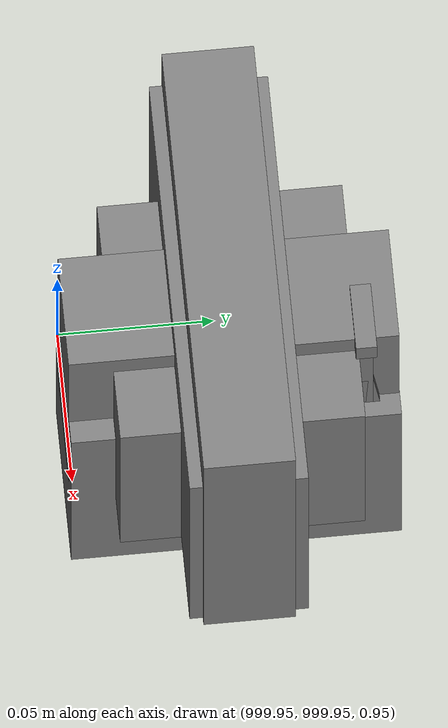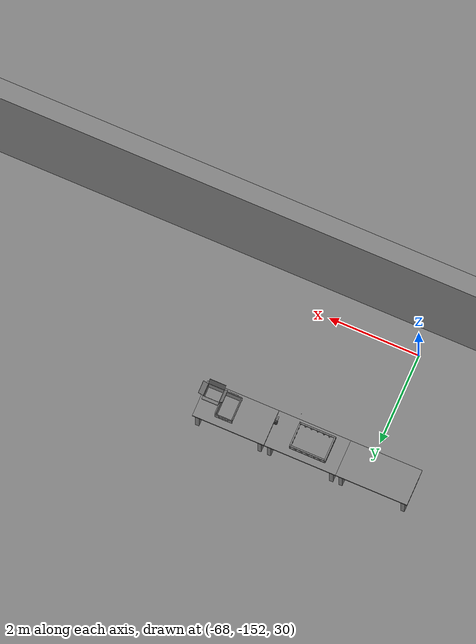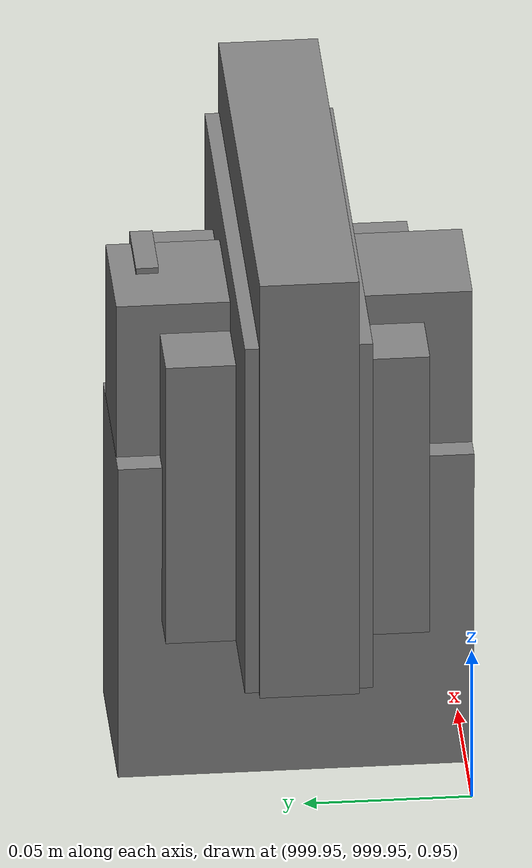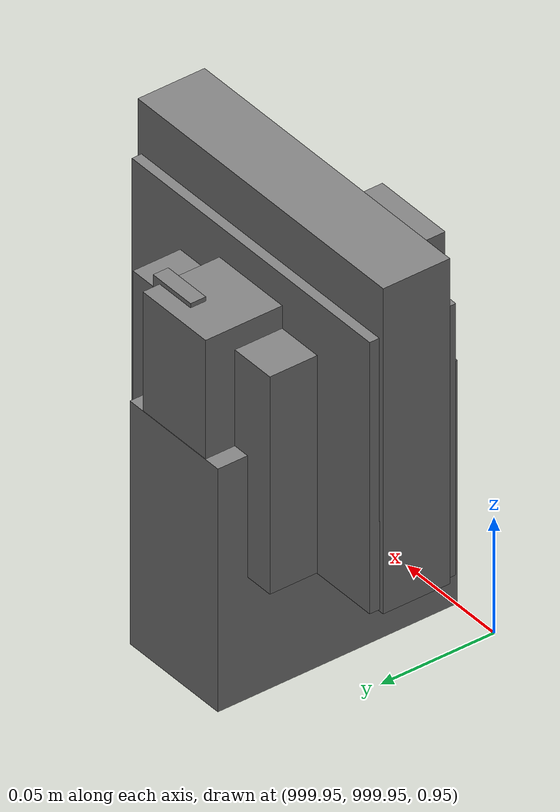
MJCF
<mujoco>
    <option gravity="0.000000000 0.000000000 -9.810000420" timestep="0.0049999999" integrator="implicitfast" density="1.225" viscosity="1.8000001e-05" noslip_iterations="10" iterations="100" sdf_iterations="50">
        <flag multiccd="disable"/>
    </option>
    <size memory="1000M"/>
    <compiler coordinate="local"/>
    <worldbody>
        <light cutoff="30" pos="0 1 1" dir="0 -1 -2"/>
        <light cutoff="30" pos="0 -1 1" dir="0 1 -2"/>
        <body pos="1000.000000000 1000.000000000 1.000000000" euler="0.000000000 0.000000000 180.000000000" name="openloong_gripper_2f85_fix_base_usda_cpu_fan">
            <geom contype="1" conaffinity="1" density="1000" type="box" material="" rgba="0.500000000 0.500000000 0.500000000 1.000000000" solimp="0.899999976 0.949999988 0.001000000" friction="1.000000000 0.005000000 0.000100000" solref="0.020000000 1.000000000" margin="0" condim="3" group="0" pos="0.000000000 0.000000000 0.070034981" quat="0.000000000 0.000000000 0.000000000 1.000000000" size="0.070700005 0.014699999 0.070700005" name="openloong_gripper_2f85_fix_base_usda_geom_F08C3EAF_1D45_4693_98F7_4BA99F238006"/>
            <freejoint name="openloong_gripper_2f85_fix_base_usda_cpu_fan_joint"/>
            <site size="0.005000000 0.005000000 0.005000000" rgba="0.500000000 0.500000000 0.500000000 1.000000000" pos="0.000000000 0.000000000 0.000000000" quat="0.999961913 0.008726535 0.000000000 0.000000000" group="0" type="sphere" name="openloong_gripper_2f85_fix_base_usda_cpu_fancsite"/>
        </body>
        <body pos="1000.000000000 1000.000000000 1.000000000" euler="0.000000000 0.000000000 180.000000000" name="openloong_gripper_2f85_fix_base_usda_wifi_box">
            <geom contype="1" conaffinity="1" density="1000" type="box" material="" rgba="0.500000000 0.500000000 0.500000000 1.000000000" solimp="0.899999976 0.949999988 0.001000000" friction="1.000000000 0.005000000 0.000100000" solref="0.020000000 1.000000000" margin="0" condim="3" group="0" pos="0.000000000 0.000000000 0.058978677" quat="0.000000000 0.000000047 0.000000000 1.000000000" size="0.068499997 0.018999999 0.059000000" name="openloong_gripper_2f85_fix_base_usda_geom_6DFF18C5_002A_49BF_9426_B0523AB9FECC"/>
            <freejoint name="openloong_gripper_2f85_fix_base_usda_wifi_box_joint"/>
            <site size="0.005000000 0.005000000 0.005000000" rgba="0.500000000 0.500000000 0.500000000 1.000000000" pos="0.000000000 0.000000000 0.000000000" quat="0.999961913 0.008726500 0.000000000 0.000000000" group="0" type="sphere" name="openloong_gripper_2f85_fix_base_usda_wifi_boxsite"/>
        </body>
        <body pos="1000.000000000 1000.000000000 1.000000000" euler="0.000000000 0.000000000 180.000000000" name="openloong_gripper_2f85_fix_base_usda_battery_01">
            <geom contype="1" conaffinity="1" density="1000" type="box" material="" rgba="0.500000000 0.500000000 0.500000000 1.000000000" solimp="0.899999976 0.949999988 0.001000000" friction="1.000000000 0.005000000 0.000100000" solref="0.020000000 1.000000000" margin="0" condim="3" group="0" pos="-0.011123657 -0.041940309 0.101691343" quat="1.000000000 0.000000000 0.000000000 0.000000000" size="0.010800000 0.003375000 0.004725000" name="openloong_gripper_2f85_fix_base_usda_geom_6E1A7CA2_352C_4315_9B1F_12AD62F93F09"/>
            <geom contype="1" conaffinity="1" density="1000" type="box" material="" rgba="0.500000000 0.500000000 0.500000000 1.000000000" solimp="0.899999976 0.949999988 0.001000000" friction="1.000000000 0.005000000 0.000100000" solref="0.020000000 1.000000000" margin="0" condim="3" group="0" pos="-0.010876465 -0.044247437 0.047066893" quat="0.998702705 -0.050920475 0.000000000 0.000000000" size="0.009450001 0.002700000 0.024975000" name="openloong_gripper_2f85_fix_base_usda_geom_30C6694A_69E4_4052_8A92_75775A2FB504"/>
            <geom contype="1" conaffinity="1" density="1000" type="box" material="" rgba="0.500000000 0.500000000 0.500000000 1.000000000" solimp="0.899999976 0.949999988 0.001000000" friction="1.000000000 0.005000000 0.000100000" solref="0.020000000 1.000000000" margin="0" condim="3" group="0" pos="-0.001235962 -0.000659180 0.047381196" quat="1.000000000 0.000000000 0.000000000 0.000000000" size="0.039420001 0.039150000 0.047250003" name="openloong_gripper_2f85_fix_base_usda_geom_F4469869_4BE3_495D_BFDD_5250C68C36CC"/>
            <geom contype="1" conaffinity="1" density="1000" type="box" material="" rgba="0.500000000 0.500000000 0.500000000 1.000000000" solimp="0.899999976 0.949999988 0.001000000" friction="1.000000000 0.005000000 0.000100000" solref="0.020000000 1.000000000" margin="0" condim="3" group="0" pos="-0.010876465 -0.039138794 0.009851727" quat="1.000000000 0.000000000 0.000000000 0.000000000" size="0.009450001 0.010800000 0.013500000" name="openloong_gripper_2f85_fix_base_usda_geom_73A11967_006E_4E1B_85A8_FFEEEEC40A1F"/>
            <geom contype="1" conaffinity="1" density="1000" type="box" material="" rgba="0.500000000 0.500000000 0.500000000 1.000000000" solimp="0.899999976 0.949999988 0.001000000" friction="1.000000000 0.005000000 0.000100000" solref="0.020000000 1.000000000" margin="0" condim="3" group="0" pos="-0.010876465 -0.041528322 0.071508206" quat="1.000000000 0.000000000 0.000000000 0.000000000" size="0.009450001 0.002700000 0.027000001" name="openloong_gripper_2f85_fix_base_usda_geom_CD650E1B_B051_4A13_A9CE_25F6327A04EC"/>
            <freejoint name="openloong_gripper_2f85_fix_base_usda_battery_01_joint"/>
            <site size="0.005000000 0.005000000 0.005000000" rgba="0.500000000 0.500000000 0.500000000 1.000000000" pos="0.000000000 0.000000000 0.000000000" quat="0.999961913 0.008726500 0.000000000 0.000000000" group="0" type="sphere" name="openloong_gripper_2f85_fix_base_usda_battery_01site"/>
        </body>
        <body pos="1000.000000000 1000.000000000 1.000000000" euler="0.000011953 0.000005123 -179.999984741" name="openloong_gripper_2f85_fix_base_usda_intel_box">
            <geom contype="1" conaffinity="1" density="1000" type="box" material="" rgba="0.500000000 0.500000000 0.500000000 1.000000000" solimp="0.899999976 0.949999988 0.001000000" friction="1.000000000 0.005000000 0.000100000" solref="0.020000000 1.000000000" margin="0" condim="3" group="0" pos="0.000000000 -0.000067139 0.000082284" quat="0.707106709 0.000000225 0.000000253 0.707106650" size="0.052800003 0.025300000 0.052800003" name="openloong_gripper_2f85_fix_base_usda_geom_49DAA91D_9FE7_4C8B_A8BD_A0A44836C42F"/>
            <freejoint name="openloong_gripper_2f85_fix_base_usda_intel_box_joint"/>
            <site size="0.005000000 0.005000000 0.005000000" rgba="0.500000000 0.500000000 0.500000000 1.000000000" pos="0.000000000 0.000000000 0.000000000" quat="0.999961913 0.008726500 0.000000000 0.000000000" group="0" type="sphere" name="openloong_gripper_2f85_fix_base_usda_intel_boxsite"/>
        </body>
        <body pos="-66.255538940 -149.682556152 31.171245575" euler="-80.054267883 -2.469662905 -94.798828125" mocap="true" name="spotlight5_SpotLight"/>
        <body pos="1000.000000000 999.999938965 1.000000000" euler="0.000000000 0.000000000 180.000000000" name="openloong_gripper_2f85_fix_base_usda_intelcore_i5">
            <geom contype="1" conaffinity="1" density="1000" type="box" material="" rgba="0.500000000 0.500000000 0.500000000 1.000000000" solimp="0.899999976 0.949999988 0.001000000" friction="1.000000000 0.005000000 0.000100000" solref="0.020000000 1.000000000" margin="0" condim="3" group="0" pos="0.000000000 0.000000000 0.051722717" quat="0.707106709 0.000000000 0.000000000 -0.707106769" size="0.052800000 0.018080002 0.052800000" name="openloong_gripper_2f85_fix_base_usda_geom_3073A848_87E0_4B79_AA49_6B0DD9588A33"/>
            <freejoint name="openloong_gripper_2f85_fix_base_usda_intelcore_i5_joint"/>
            <site size="0.005000000 0.005000000 0.005000000" rgba="0.500000000 0.500000000 0.500000000 1.000000000" pos="0.000000000 0.000000000 0.000000000" quat="0.999961913 0.008726534 0.000000000 0.000000000" group="0" type="sphere" name="openloong_gripper_2f85_fix_base_usda_intelcore_i5site"/>
        </body>
        <body pos="-66.111953735 -149.451461792 31.171329498" euler="63.200241089 -29.049486160 76.912239075" mocap="true" name="spotlight2_SpotLight"/>
        <body pos="-66.363594055 -149.684860229 31.164756775" euler="75.885017395 -48.984600067 -119.581275940" mocap="true" name="spotlight1_SpotLight"/>
        <body pos="-64.866622925 -149.383972168 30.183746338" euler="89.999984741 89.999946594 0.000000000" name="openloong_gripper_2f85_fix_base_usda_bluebox_01">
            <geom contype="1" conaffinity="1" density="1000" type="box" material="" rgba="0.500000000 0.500000000 0.500000000 1.000000000" solimp="0.899999976 0.949999988 0.001000000" friction="1.000000000 0.005000000 0.000100000" solref="0.020000000 1.000000000" margin="0" condim="3" group="0" pos="0.276580811 0.187225342 0.000068665" quat="0.707106948 0.000077471 0.707106352 0.000077486" size="0.100000001 0.057999998 0.010000000" name="openloong_gripper_2f85_fix_base_usda_geom_E4E24343_A8FE_4FAA_ADE9_C8182424A393"/>
            <geom contype="1" conaffinity="1" density="1000" type="box" material="" rgba="0.500000000 0.500000000 0.500000000 1.000000000" solimp="0.899999976 0.949999988 0.001000000" friction="1.000000000 0.005000000 0.000100000" solref="0.020000000 1.000000000" margin="0" condim="3" group="0" pos="0.000000000 0.002883911 0.000000000" quat="0.999999881 0.000000000 0.000000000 0.000000000" size="0.254000008 0.003000000 0.172000006" name="openloong_gripper_2f85_fix_base_usda_geom_CF74E91A_4357_41D8_9A62_7743AAC2C159"/>
            <geom contype="1" conaffinity="1" density="1000" type="box" material="" rgba="0.500000000 0.500000000 0.500000000 1.000000000" solimp="0.899999976 0.949999988 0.001000000" friction="1.000000000 0.005000000 0.000100000" solref="0.020000000 1.000000000" margin="0" condim="3" group="0" pos="0.000000000 0.124874115 0.173484802" quat="0.999796331 0.020176515 -0.000000015 0.000000030" size="0.259999990 0.119999997 0.007000000" name="openloong_gripper_2f85_fix_base_usda_geom_7EE73D74_A898_4778_BF79_3148FCF5F937"/>
            <geom contype="1" conaffinity="1" density="1000" type="box" material="" rgba="0.500000000 0.500000000 0.500000000 1.000000000" solimp="0.899999976 0.949999988 0.001000000" friction="1.000000000 0.005000000 0.000100000" solref="0.020000000 1.000000000" margin="0" condim="3" group="0" pos="0.000000000 0.124874115 -0.173469543" quat="0.999796331 -0.020176545 -0.000000015 0.000000000" size="0.259999990 0.119999997 0.007000000" name="openloong_gripper_2f85_fix_base_usda_geom_056A06D3_C2FA_4B40_BB62_E49A3CC97A3C"/>
            <geom contype="1" conaffinity="1" density="1000" type="box" material="" rgba="0.500000000 0.500000000 0.500000000 1.000000000" solimp="0.899999976 0.949999988 0.001000000" friction="1.000000000 0.005000000 0.000100000" solref="0.020000000 1.000000000" margin="0" condim="3" group="0" pos="0.000000000 0.214008331 0.188980103" quat="0.999912977 0.013176724 0.000000015 0.000000000" size="0.259999990 0.029999999 0.012500000" name="openloong_gripper_2f85_fix_base_usda_geom_1A244633_AB38_4703_97C0_A1C24FCB9A42"/>
            <geom contype="1" conaffinity="1" density="1000" type="box" material="" rgba="0.500000000 0.500000000 0.500000000 1.000000000" solimp="0.899999976 0.949999988 0.001000000" friction="1.000000000 0.005000000 0.000100000" solref="0.020000000 1.000000000" margin="0" condim="3" group="0" pos="-0.258361816 0.125289917 0.001876831" quat="0.702796936 -0.020792112 0.710783124 0.020769298" size="0.189999998 0.119999997 0.009000000" name="openloong_gripper_2f85_fix_base_usda_geom_7F45408A_B8C8_4A5F_A1DB_41123BFBCAE0"/>
            <geom contype="1" conaffinity="1" density="1000" type="box" material="" rgba="0.500000000 0.500000000 0.500000000 1.000000000" solimp="0.899999976 0.949999988 0.001000000" friction="1.000000000 0.005000000 0.000100000" solref="0.020000000 1.000000000" margin="0" condim="3" group="0" pos="0.000000000 0.214008331 -0.188980103" quat="0.999912977 -0.013176769 0.000000030 0.000000015" size="0.259999990 0.029999999 0.012500000" name="openloong_gripper_2f85_fix_base_usda_geom_89ACF6E9_0FAB_4C27_849A_14757AE570A7"/>
            <geom contype="1" conaffinity="1" density="1000" type="box" material="" rgba="0.500000000 0.500000000 0.500000000 1.000000000" solimp="0.899999976 0.949999988 0.001000000" friction="1.000000000 0.005000000 0.000100000" solref="0.020000000 1.000000000" margin="0" condim="3" group="0" pos="-0.276611328 0.187225342 0.000068665" quat="0.707106650 0.000077441 0.707106709 0.000077456" size="0.100000001 0.057999998 0.010000000" name="openloong_gripper_2f85_fix_base_usda_geom_222F0378_2735_42D0_9FEB_6D7EE88DBC2D"/>
            <geom contype="1" conaffinity="1" density="1000" type="box" material="" rgba="0.500000000 0.500000000 0.500000000 1.000000000" solimp="0.899999976 0.949999988 0.001000000" friction="1.000000000 0.005000000 0.000100000" solref="0.020000000 1.000000000" margin="0" condim="3" group="0" pos="0.258331299 0.125289917 0.001876831" quat="0.702851415 0.018856421 0.710823774 -0.019329369" size="0.189999998 0.119999997 0.009000000" name="openloong_gripper_2f85_fix_base_usda_geom_6A027F8D_3618_4A3F_A529_7FCE5C8772B6"/>
            <freejoint name="openloong_gripper_2f85_fix_base_usda_bluebox_01_joint"/>
            <site size="0.005000000 0.005000000 0.005000000" rgba="0.500000000 0.500000000 0.500000000 1.000000000" pos="0.000000000 0.000000000 0.000000000" quat="0.999961913 0.008726534 0.000000000 0.000000000" group="0" type="sphere" name="openloong_gripper_2f85_fix_base_usda_bluebox_01site"/>
        </body>
        <body pos="-64.496299744 -149.491867065 30.235729218" euler="0.000000000 0.000000000 89.999946594" name="openloong_gripper_2f85_fix_base_usda_cardboardbox_01">
            <geom contype="1" conaffinity="1" density="1000" type="box" material="" rgba="0.500000000 0.500000000 0.500000000 1.000000000" solimp="0.899999976 0.949999988 0.001000000" friction="1.000000000 0.005000000 0.000100000" solref="0.020000000 1.000000000" margin="0" condim="3" group="0" pos="-0.003166199 -0.004086494 0.005052090" quat="1.000000000 0.000000000 0.000000000 0.000000000" size="0.142499998 0.177500010 0.005000000" name="openloong_gripper_2f85_fix_base_usda_geom_58A92909_D5EF_4216_903B_13B37DDB2D13"/>
            <geom contype="1" conaffinity="1" density="1000" type="box" material="" rgba="0.500000000 0.500000000 0.500000000 1.000000000" solimp="0.899999976 0.949999988 0.001000000" friction="1.000000000 0.005000000 0.000100000" solref="0.020000000 1.000000000" margin="0" condim="3" group="0" pos="-0.003166199 0.170316696 0.150570869" quat="1.000000000 0.000000000 0.000000000 0.000000000" size="0.142499998 0.005000000 0.149999991" name="openloong_gripper_2f85_fix_base_usda_geom_9B4BB475_7120_4BF8_8A7C_5FFF324933DE"/>
            <geom contype="1" conaffinity="1" density="1000" type="box" material="" rgba="0.500000000 0.500000000 0.500000000 1.000000000" solimp="0.899999976 0.949999988 0.001000000" friction="1.000000000 0.005000000 0.000100000" solref="0.020000000 1.000000000" margin="0" condim="3" group="0" pos="-0.147399902 -0.005307198 0.150570869" quat="1.000000000 0.000000000 0.000000000 0.000000000" size="0.005000000 0.177500010 0.149999991" name="openloong_gripper_2f85_fix_base_usda_geom_E8132327_E987_4E26_A638_ACD95B821F26"/>
            <geom contype="1" conaffinity="1" density="1000" type="box" material="" rgba="0.500000000 0.500000000 0.500000000 1.000000000" solimp="0.899999976 0.949999988 0.001000000" friction="1.000000000 0.005000000 0.000100000" solref="0.020000000 1.000000000" margin="0" condim="3" group="0" pos="0.140275955 -0.005307198 0.150570869" quat="1.000000000 0.000000000 0.000000000 0.000000000" size="0.005000000 0.177500010 0.149999991" name="openloong_gripper_2f85_fix_base_usda_geom_7B226347_1EEC_4137_993E_908F5E66C396"/>
            <geom contype="1" conaffinity="1" density="1000" type="box" material="" rgba="0.500000000 0.500000000 0.500000000 1.000000000" solimp="0.899999976 0.949999988 0.001000000" friction="1.000000000 0.005000000 0.000100000" solref="0.020000000 1.000000000" margin="0" condim="3" group="0" pos="-0.003166199 -0.181550980 0.150570869" quat="1.000000000 0.000000000 0.000000000 0.000000000" size="0.142499998 0.005000000 0.149999991" name="openloong_gripper_2f85_fix_base_usda_geom_8C9A99DC_DA8F_4E42_9C2C_B76B4A6E6574"/>
            <freejoint name="openloong_gripper_2f85_fix_base_usda_cardboardbox_01_joint"/>
            <site size="0.005000000 0.005000000 0.005000000" rgba="0.500000000 0.500000000 0.500000000 1.000000000" pos="0.000000000 0.000000000 0.000000000" quat="0.999961913 0.008726535 0.000000000 0.000000000" group="0" type="sphere" name="openloong_gripper_2f85_fix_base_usda_site_38AC6C2E_0FA3_476A_8050_080A0F17F24B"/>
            <body pos="0.139160156 -0.004048347 0.301930904" euler="-179.999954224 49.383502960 179.999954224" name="openloong_gripper_2f85_fix_base_usda_A1_006">
                <geom contype="1" conaffinity="1" density="1000" type="box" material="" rgba="0.500000000 0.500000000 0.500000000 1.000000000" solimp="0.899999976 0.949999988 0.001000000" friction="1.000000000 0.005000000 0.000100000" solref="0.020000000 1.000000000" margin="0" condim="3" group="0" pos="-0.071587563 0.000009537 0.001745224" quat="0.999999881 0.000000000 0.000000000 0.000000000" size="0.071249999 0.179999992 0.002500000" name="openloong_gripper_2f85_fix_base_usda_geom_657E5011_6C69_4C68_ABB4_8DDD1C6D8855"/>
                <joint armature="0" stiffness="0.07" damping="0.0099999998" axis="0.000000 1.000000 0.000000" type="hinge" name="openloong_gripper_2f85_fix_base_usda_A1_006"/>
            </body>
            <body pos="-0.145902634 -0.004086494 0.301938057" euler="-180.000000000 -60.000011444 -180.000000000" name="openloong_gripper_2f85_fix_base_usda_A2_006">
                <geom contype="1" conaffinity="1" density="1000" type="box" material="" rgba="0.500000000 0.500000000 0.500000000 1.000000000" solimp="0.899999976 0.949999988 0.001000000" friction="1.000000000 0.005000000 0.000100000" solref="0.020000000 1.000000000" margin="0" condim="3" group="0" pos="0.071268082 0.000009537 0.002717972" quat="0.000002921 0.000000000 -0.000000030 0.999999881" size="0.071249999 0.179999992 0.002500000" name="openloong_gripper_2f85_fix_base_usda_geom_20A62F47_71DE_4AEC_A118_D15EE6516F25"/>
                <joint armature="0" stiffness="0.07" damping="0.0099999998" axis="0.000000 1.000000 0.000000" type="hinge" name="openloong_gripper_2f85_fix_base_usda_A2_006"/>
            </body>
            <body pos="-0.003385544 0.175991058 0.301930904" euler="-125.858116150 -0.000004561 0.000002331" name="openloong_gripper_2f85_fix_base_usda_B2_006">
                <geom contype="1" conaffinity="1" density="1000" type="box" material="" rgba="0.500000000 0.500000000 0.500000000 1.000000000" solimp="0.899999976 0.949999988 0.001000000" friction="1.000000000 0.005000000 0.000100000" solref="0.020000000 1.000000000" margin="0" condim="3" group="0" pos="0.000009537 -0.070939064 -0.002470016" quat="0.999614120 0.027776197 -0.000000015 0.000000030" size="0.137500003 0.064999998 0.005000000" name="openloong_gripper_2f85_fix_base_usda_geom_14F131BB_9483_421A_A205_FF30949E6CEB"/>
                <joint armature="0" stiffness="0.07" damping="0.0099999998" axis="1.000000 0.000000 0.000000" type="hinge" name="openloong_gripper_2f85_fix_base_usda_B2_006"/>
            </body>
            <body pos="-0.003385544 -0.184140205 0.301938057" euler="147.805557251 0.000000000 0.000000000" name="openloong_gripper_2f85_fix_base_usda_B1_006">
                <geom contype="1" conaffinity="1" density="1000" type="box" material="" rgba="0.500000000 0.500000000 0.500000000 1.000000000" solimp="0.899999976 0.949999988 0.001000000" friction="1.000000000 0.005000000 0.000100000" solref="0.020000000 1.000000000" margin="0" condim="3" group="0" pos="-0.000028610 0.070202351 -0.002703667" quat="0.999614179 -0.027776167 0.000000000 0.000000000" size="0.137500003 0.064999998 0.005000000" name="openloong_gripper_2f85_fix_base_usda_geom_757759FF_A32A_4A43_8B0C_AAF7FE133889"/>
                <joint armature="0" stiffness="0.07" damping="0.0099999998" axis="1.000000 0.000000 0.000000" type="hinge" name="openloong_gripper_2f85_fix_base_usda_B1_006"/>
            </body>
        </body>
        <body pos="-65.882858276 -149.481979370 30.229999542" euler="-64.487716675 0.000000000 0.000000000" name="openloong_gripper_2f85_fix_base_usda_Barcode">
            <geom contype="1" conaffinity="1" density="1000" type="box" material="" rgba="0.500000000 0.500000000 0.500000000 1.000000000" solimp="0.899999976 0.949999988 0.001000000" friction="1.000000000 0.005000000 0.000100000" solref="0.020000000 1.000000000" margin="0" condim="3" group="0" pos="0.000000000 0.013038635 0.001419067" quat="0.000000000 0.000000000 0.000000000 1.000000119" size="0.034000002 0.010000000 0.017999999" name="openloong_gripper_2f85_fix_base_usda_geom_FA9615D4_A7C7_472E_9ECD_57F5C2A07813"/>
            <geom contype="1" conaffinity="1" density="1000" type="box" material="" rgba="0.500000000 0.500000000 0.500000000 1.000000000" solimp="0.899999976 0.949999988 0.001000000" friction="1.000000000 0.005000000 0.000100000" solref="0.020000000 1.000000000" margin="0" condim="3" group="0" pos="0.000000000 -0.035301208 -0.007095337" quat="0.000000000 0.000000000 -0.043619365 0.999048233" size="0.028999999 0.010000000 0.020000000" name="openloong_gripper_2f85_fix_base_usda_geom_992F0DBC_3A50_41D5_BC54_C6E212295A01"/>
            <geom contype="1" conaffinity="1" density="1000" type="box" material="" rgba="0.500000000 0.500000000 0.500000000 1.000000000" solimp="0.899999976 0.949999988 0.001000000" friction="1.000000000 0.005000000 0.000100000" solref="0.020000000 1.000000000" margin="0" condim="3" group="0" pos="0.000000000 -0.043411255 -0.011749268" quat="0.922262907 0.386563420 0.000000000 0.000000000" size="0.026000001 0.010000000 0.020000000" name="openloong_gripper_2f85_fix_base_usda_geom_E58DB0D5_8B39_4FD7_B197_E3A046361DBE"/>
            <geom contype="1" conaffinity="1" density="1000" type="box" material="" rgba="0.500000000 0.500000000 0.500000000 1.000000000" solimp="0.899999976 0.949999988 0.001000000" friction="1.000000000 0.005000000 0.000100000" solref="0.020000000 1.000000000" margin="0" condim="3" group="0" pos="0.000000000 -0.016967773 -0.031860352" quat="0.000000000 0.000000000 0.000000000 1.000000119" size="0.008000000 0.010000000 0.013000000" name="openloong_gripper_2f85_fix_base_usda_geom_DA6490BF_7FBC_42DA_99D4_80597AE33B08"/>
            <geom contype="1" conaffinity="1" density="1000" type="box" material="" rgba="0.500000000 0.500000000 0.500000000 1.000000000" solimp="0.899999976 0.949999988 0.001000000" friction="1.000000000 0.005000000 0.000100000" solref="0.020000000 1.000000000" margin="0" condim="3" group="0" pos="0.000000000 -0.001869202 0.000312805" quat="0.953716993 0.300705761 0.000000000 0.000000000" size="0.032000002 0.010000000 0.018999999" name="openloong_gripper_2f85_fix_base_usda_geom_3E81B84A_F5D5_4E4A_9831_3FA965E98F2E"/>
            <geom contype="1" conaffinity="1" density="1000" type="box" material="" rgba="0.500000000 0.500000000 0.500000000 1.000000000" solimp="0.899999976 0.949999988 0.001000000" friction="1.000000000 0.005000000 0.000100000" solref="0.020000000 1.000000000" margin="0" condim="3" group="0" pos="0.000000000 -0.019531250 -0.003173828" quat="0.953716993 0.300705761 0.000000000 0.000000000" size="0.030999999 0.010000000 0.020000000" name="openloong_gripper_2f85_fix_base_usda_geom_409EF362_1520_4C48_BCAA_5C5E5FD3A397"/>
            <geom contype="1" conaffinity="1" density="1000" type="box" material="" rgba="0.500000000 0.500000000 0.500000000 1.000000000" solimp="0.899999976 0.949999988 0.001000000" friction="1.000000000 0.005000000 0.000100000" solref="0.020000000 1.000000000" margin="0" condim="3" group="0" pos="0.000000000 -0.035301208 -0.007095337" quat="0.953716993 0.300705761 0.000000000 0.000000000" size="0.028999999 0.010000000 0.020000000" name="openloong_gripper_2f85_fix_base_usda_geom_3DF83DC3_B4ED_48AA_B44E_A4EDBD803881"/>
            <geom contype="1" conaffinity="1" density="1000" type="box" material="" rgba="0.500000000 0.500000000 0.500000000 1.000000000" solimp="0.899999976 0.949999988 0.001000000" friction="1.000000000 0.005000000 0.000100000" solref="0.020000000 1.000000000" margin="0" condim="3" group="0" pos="0.000000000 -0.042617798 -0.071121216" quat="0.000000000 0.000000000 0.000000000 1.000000119" size="0.013000000 0.021000000 0.059999999" name="openloong_gripper_2f85_fix_base_usda_geom_D4B801FA_B330_4D4F_9819_B817A15FE653"/>
            <freejoint name="openloong_gripper_2f85_fix_base_usda_Barcode_joint"/>
            <site size="0.005000000 0.005000000 0.005000000" rgba="0.500000000 0.500000000 0.500000000 1.000000000" pos="0.000000000 0.000000000 0.000000000" quat="1.000000000 0.000000000 0.000000000 0.000000000" group="0" type="sphere" name="openloong_gripper_2f85_fix_base_usda_Barcode_site"/>
        </body>
        <body pos="-66.745018005 -149.392349243 30.184000015" euler="0.000000000 0.000000000 89.999946594" name="[22331289095382]_Basket_01">
            <geom contype="1" conaffinity="1" density="1000" type="box" material="" rgba="0.500000000 0.500000000 0.500000000 1.000000000" solimp="0.899999976 0.949999988 0.001000000" friction="1.000000000 0.005000000 0.000100000" solref="0.020000000 1.000000000" margin="0" condim="3" group="0" pos="-0.052425385 0.389207840 0.089787483" quat="0.707107008 0.000000000 0.000000000 0.707106411" size="0.014249999 0.014249999 0.059999999" name="[22331289095382]_geom_646D6FD5_1803_4109_8612_E564723973EA"/>
            <geom contype="1" conaffinity="1" density="1000" type="box" material="" rgba="0.500000000 0.500000000 0.500000000 1.000000000" solimp="0.899999976 0.949999988 0.001000000" friction="1.000000000 0.005000000 0.000100000" solref="0.020000000 1.000000000" margin="0" condim="3" group="0" pos="0.264015198 -0.133043289 0.089787483" quat="0.707107008 0.000000000 0.000000000 0.707106411" size="0.014249999 0.014249999 0.059999999" name="[22331289095382]_geom_00FD4031_F3CD_429F_9873_51091E7DA283"/>
            <geom contype="1" conaffinity="1" density="1000" type="box" material="" rgba="0.500000000 0.500000000 0.500000000 1.000000000" solimp="0.899999976 0.949999988 0.001000000" friction="1.000000000 0.005000000 0.000100000" solref="0.020000000 1.000000000" margin="0" condim="3" group="0" pos="-0.264015198 -0.265548706 0.089793205" quat="0.707107008 0.000000000 0.000000000 0.707106411" size="0.014249999 0.014249999 0.059999999" name="[22331289095382]_geom_D8995325_EE61_4E61_81CF_B8502D482EDA"/>
            <geom contype="1" conaffinity="1" density="1000" type="box" material="" rgba="0.500000000 0.500000000 0.500000000 1.000000000" solimp="0.899999976 0.949999988 0.001000000" friction="1.000000000 0.005000000 0.000100000" solref="0.020000000 1.000000000" margin="0" condim="3" group="0" pos="-0.160263062 -0.389322281 0.089793205" quat="0.707107008 0.000000000 0.000000000 0.707106411" size="0.014249999 0.014249999 0.059999999" name="[22331289095382]_geom_D46408DB_AD57_4D15_A41B_D274FE710F20"/>
            <geom contype="1" conaffinity="1" density="1000" type="box" material="" rgba="0.500000000 0.500000000 0.500000000 1.000000000" solimp="0.899999976 0.949999988 0.001000000" friction="1.000000000 0.005000000 0.000100000" solref="0.020000000 1.000000000" margin="0" condim="3" group="0" pos="0.162265778 -0.389322281 0.089787483" quat="0.707107008 0.000000000 0.000000000 0.707106411" size="0.014249999 0.014249999 0.059999999" name="[22331289095382]_geom_5341C231_D64C_4A13_ABE7_F5F451299415"/>
            <geom contype="1" conaffinity="1" density="1000" type="box" material="" rgba="0.500000000 0.500000000 0.500000000 1.000000000" solimp="0.899999976 0.949999988 0.001000000" friction="1.000000000 0.005000000 0.000100000" solref="0.020000000 1.000000000" margin="0" condim="3" group="0" pos="0.264015198 0.389207840 0.089787483" quat="0.707107008 0.000000000 0.000000000 0.707106411" size="0.014249999 0.014249999 0.059999999" name="[22331289095382]_geom_E5134052_F2DF_4D8C_B4DA_258AD21C5B34"/>
            <geom contype="1" conaffinity="1" density="1000" type="box" material="" rgba="0.500000000 0.500000000 0.500000000 1.000000000" solimp="0.899999976 0.949999988 0.001000000" friction="1.000000000 0.005000000 0.000100000" solref="0.020000000 1.000000000" margin="0" condim="3" group="0" pos="-0.264015198 -0.133043289 0.089793205" quat="0.707107008 0.000000000 0.000000000 0.707106411" size="0.014249999 0.014249999 0.059999999" name="[22331289095382]_geom_26065F95_58AE_4EB3_B3B4_BE2779C7BF5D"/>
            <geom contype="1" conaffinity="1" density="1000" type="box" material="" rgba="0.500000000 0.500000000 0.500000000 1.000000000" solimp="0.899999976 0.949999988 0.001000000" friction="1.000000000 0.005000000 0.000100000" solref="0.020000000 1.000000000" margin="0" condim="3" group="0" pos="-0.264026642 0.269256592 0.089793205" quat="0.707107008 0.000000000 0.000000000 0.707106411" size="0.014249999 0.014249999 0.059999999" name="[22331289095382]_geom_F5BB8949_9E0D_4845_AFDA_8B5AD8501F8C"/>
            <geom contype="1" conaffinity="1" density="1000" type="box" material="" rgba="0.500000000 0.500000000 0.500000000 1.000000000" solimp="0.899999976 0.949999988 0.001000000" friction="1.000000000 0.005000000 0.000100000" solref="0.020000000 1.000000000" margin="0" condim="3" group="0" pos="0.054462433 0.389207840 0.089787483" quat="0.707107008 0.000000000 0.000000000 0.707106411" size="0.014249999 0.014249999 0.059999999" name="[22331289095382]_geom_C8B819C8_F503_4F7C_B7FA_2158ABED34F2"/>
            <geom contype="1" conaffinity="1" density="1000" type="box" material="" rgba="0.500000000 0.500000000 0.500000000 1.000000000" solimp="0.899999976 0.949999988 0.001000000" friction="1.000000000 0.005000000 0.000100000" solref="0.020000000 1.000000000" margin="0" condim="3" group="0" pos="0.054462433 -0.389322281 0.089787483" quat="0.707107008 0.000000000 0.000000000 0.707106411" size="0.014249999 0.014249999 0.059999999" name="[22331289095382]_geom_D2A9A564_E543_4932_9E02_E7FEBFC04C8C"/>
            <geom contype="1" conaffinity="1" density="1000" type="box" material="" rgba="0.500000000 0.500000000 0.500000000 1.000000000" solimp="0.899999976 0.949999988 0.001000000" friction="1.000000000 0.005000000 0.000100000" solref="0.020000000 1.000000000" margin="0" condim="3" group="0" pos="0.264015198 0.269256592 0.089793205" quat="0.707107008 0.000000000 0.000000000 0.707106411" size="0.014249999 0.014249999 0.059999999" name="[22331289095382]_geom_E4B2DFC7_73D2_48C6_90DB_568CE12BDDB4"/>
            <geom contype="1" conaffinity="1" density="1000" type="box" material="" rgba="0.500000000 0.500000000 0.500000000 1.000000000" solimp="0.899999976 0.949999988 0.001000000" friction="1.000000000 0.005000000 0.000100000" solref="0.020000000 1.000000000" margin="0" condim="3" group="0" pos="0.264015198 -0.389322281 0.089787483" quat="0.707107008 0.000000000 0.000000000 0.707106411" size="0.014249999 0.014249999 0.059999999" name="[22331289095382]_geom_B65EBAA8_0F2E_4E76_822D_19251602C457"/>
            <geom contype="1" conaffinity="1" density="1000" type="box" material="" rgba="0.500000000 0.500000000 0.500000000 1.000000000" solimp="0.899999976 0.949999988 0.001000000" friction="1.000000000 0.005000000 0.000100000" solref="0.020000000 1.000000000" margin="0" condim="3" group="0" pos="0.000000000 0.000000000 0.015998840" quat="0.707107008 0.000000000 0.000000000 0.707106411" size="0.403499991 0.279000014 0.015750000" name="[22331289095382]_geom_5B1C950B_15EA_4B23_BFDB_73B5D5E51DF4"/>
            <geom contype="1" conaffinity="1" density="1000" type="box" material="" rgba="0.500000000 0.500000000 0.500000000 1.000000000" solimp="0.899999976 0.949999988 0.001000000" friction="1.000000000 0.005000000 0.000100000" solref="0.020000000 1.000000000" margin="0" condim="3" group="0" pos="0.000000000 -0.389476776 0.163619041" quat="0.707107008 0.000000000 0.000000000 0.707106411" size="0.015000000 0.277500004 0.015750000" name="[22331289095382]_geom_DCC7FE99_4E3B_499A_BEE1_2794977FC21F"/>
            <geom contype="1" conaffinity="1" density="1000" type="box" material="" rgba="0.500000000 0.500000000 0.500000000 1.000000000" solimp="0.899999976 0.949999988 0.001000000" friction="1.000000000 0.005000000 0.000100000" solref="0.020000000 1.000000000" margin="0" condim="3" group="0" pos="0.162265778 0.389207840 0.089787483" quat="0.707107008 0.000000000 0.000000000 0.707106411" size="0.014249999 0.014249999 0.059999999" name="[22331289095382]_geom_3EC4DC1D_4ADC_4641_9686_8072F0C4FADE"/>
            <geom contype="1" conaffinity="1" density="1000" type="box" material="" rgba="0.500000000 0.500000000 0.500000000 1.000000000" solimp="0.899999976 0.949999988 0.001000000" friction="1.000000000 0.005000000 0.000100000" solref="0.020000000 1.000000000" margin="0" condim="3" group="0" pos="0.000000000 0.389471054 0.163619041" quat="0.707107008 0.000000000 0.000000000 0.707106411" size="0.015000000 0.277500004 0.015750000" name="[22331289095382]_geom_61A0B010_61E5_43DE_917A_B1D58771B3E1"/>
            <geom contype="1" conaffinity="1" density="1000" type="box" material="" rgba="0.500000000 0.500000000 0.500000000 1.000000000" solimp="0.899999976 0.949999988 0.001000000" friction="1.000000000 0.005000000 0.000100000" solref="0.020000000 1.000000000" margin="0" condim="3" group="0" pos="-0.263511658 0.000000000 0.163619041" quat="0.707107008 0.000000000 0.000000000 0.707106411" size="0.403499991 0.015000000 0.015750000" name="[22331289095382]_geom_23FDC421_2B25_46A0_9840_FF97844B5393"/>
            <geom contype="1" conaffinity="1" density="1000" type="box" material="" rgba="0.500000000 0.500000000 0.500000000 1.000000000" solimp="0.899999976 0.949999988 0.001000000" friction="1.000000000 0.005000000 0.000100000" solref="0.020000000 1.000000000" margin="0" condim="3" group="0" pos="-0.264015198 0.141334534 0.089793205" quat="0.707107008 0.000000000 0.000000000 0.707106411" size="0.014249999 0.014249999 0.059999999" name="[22331289095382]_geom_A2B4A2FF_AED1_4F58_A606_5309BB314ABE"/>
            <geom contype="1" conaffinity="1" density="1000" type="box" material="" rgba="0.500000000 0.500000000 0.500000000 1.000000000" solimp="0.899999976 0.949999988 0.001000000" friction="1.000000000 0.005000000 0.000100000" solref="0.020000000 1.000000000" margin="0" condim="3" group="0" pos="0.264015198 -0.265548706 0.089787483" quat="0.707107008 0.000000000 0.000000000 0.707106411" size="0.014249999 0.014249999 0.059999999" name="[22331289095382]_geom_BAFC0AD2_58F0_4B15_B125_2BDA4FF3C85F"/>
            <geom contype="1" conaffinity="1" density="1000" type="box" material="" rgba="0.500000000 0.500000000 0.500000000 1.000000000" solimp="0.899999976 0.949999988 0.001000000" friction="1.000000000 0.005000000 0.000100000" solref="0.020000000 1.000000000" margin="0" condim="3" group="0" pos="-0.160263062 0.389207840 0.089787483" quat="0.707107008 0.000000000 0.000000000 0.707106411" size="0.014249999 0.014249999 0.059999999" name="[22331289095382]_geom_1E486A90_A641_4707_8B0B_2B24E144CDBD"/>
            <geom contype="1" conaffinity="1" density="1000" type="box" material="" rgba="0.500000000 0.500000000 0.500000000 1.000000000" solimp="0.899999976 0.949999988 0.001000000" friction="1.000000000 0.005000000 0.000100000" solref="0.020000000 1.000000000" margin="0" condim="3" group="0" pos="-0.052425385 -0.389322281 0.089787483" quat="0.707107008 0.000000000 0.000000000 0.707106411" size="0.014249999 0.014249999 0.059999999" name="[22331289095382]_geom_0E180A93_D982_47ED_9F29_90E3014E6FCB"/>
            <geom contype="1" conaffinity="1" density="1000" type="box" material="" rgba="0.500000000 0.500000000 0.500000000 1.000000000" solimp="0.899999976 0.949999988 0.001000000" friction="1.000000000 0.005000000 0.000100000" solref="0.020000000 1.000000000" margin="0" condim="3" group="0" pos="-0.264026642 -0.389322281 0.089793205" quat="0.707107008 0.000000000 0.000000000 0.707106411" size="0.014249999 0.014249999 0.059999999" name="[22331289095382]_geom_C78903BD_2131_4799_8FBE_3B9D05D2794D"/>
            <geom contype="1" conaffinity="1" density="1000" type="box" material="" rgba="0.500000000 0.500000000 0.500000000 1.000000000" solimp="0.899999976 0.949999988 0.001000000" friction="1.000000000 0.005000000 0.000100000" solref="0.020000000 1.000000000" margin="0" condim="3" group="0" pos="0.264015198 0.141334534 0.089787483" quat="0.707107008 0.000000000 0.000000000 0.707106411" size="0.014249999 0.014249999 0.059999999" name="[22331289095382]_geom_028C3844_826F_4AC9_98BD_19CAF50EFD69"/>
            <geom contype="1" conaffinity="1" density="1000" type="box" material="" rgba="0.500000000 0.500000000 0.500000000 1.000000000" solimp="0.899999976 0.949999988 0.001000000" friction="1.000000000 0.005000000 0.000100000" solref="0.020000000 1.000000000" margin="0" condim="3" group="0" pos="-0.264015198 0.389207840 0.089793205" quat="0.707107008 0.000000000 0.000000000 0.707106411" size="0.014249999 0.014249999 0.059999999" name="[22331289095382]_geom_F0397301_92AF_4E59_BFC5_6209615FEDE2"/>
            <geom contype="1" conaffinity="1" density="1000" type="box" material="" rgba="0.500000000 0.500000000 0.500000000 1.000000000" solimp="0.899999976 0.949999988 0.001000000" friction="1.000000000 0.005000000 0.000100000" solref="0.020000000 1.000000000" margin="0" condim="3" group="0" pos="0.264015198 0.004480362 0.089787483" quat="0.707107008 0.000000000 0.000000000 0.707106411" size="0.014249999 0.014249999 0.059999999" name="[22331289095382]_geom_D425D7F9_9544_403E_9829_D8DADFA86000"/>
            <geom contype="1" conaffinity="1" density="1000" type="box" material="" rgba="0.500000000 0.500000000 0.500000000 1.000000000" solimp="0.899999976 0.949999988 0.001000000" friction="1.000000000 0.005000000 0.000100000" solref="0.020000000 1.000000000" margin="0" condim="3" group="0" pos="0.263694763 -0.000011444 0.163619041" quat="0.707107008 0.000000000 0.000000000 0.707106411" size="0.403499991 0.015000000 0.015750000" name="[22331289095382]_geom_15C9B13F_E24E_4465_9E3A_9BC48EF90040"/>
            <geom contype="1" conaffinity="1" density="1000" type="box" material="" rgba="0.500000000 0.500000000 0.500000000 1.000000000" solimp="0.899999976 0.949999988 0.001000000" friction="1.000000000 0.005000000 0.000100000" solref="0.020000000 1.000000000" margin="0" condim="3" group="0" pos="-0.264015198 0.004480362 0.089793205" quat="0.707107008 0.000000000 0.000000000 0.707106411" size="0.014249999 0.014249999 0.059999999" name="[22331289095382]_geom_7A827EDD_A73D_436D_8E4B_A4EE36DE5CF0"/>
            <freejoint name="[22331289095382]_joint_D0211629_46F6_42F7_B495_68C9FC7F677F"/>
        </body>
        <body pos="0.000000000 0.000000000 0.000000000" euler="0.000000000 0.000000000 0.000000000" name="Static Objects_Static Objects">
            <geom contype="1" conaffinity="1" density="1000" type="box" material="" rgba="0.500000000 0.500000000 0.500000000 1.000000000" solimp="0.899999976 0.949999988 0.001000000" friction="1.000000000 0.005000000 0.000100000" solref="0.020000000 1.000000000" margin="0" condim="3" group="0" pos="-67.544113159 -149.365814209 29.727830887" quat="0.500000417 0.499999970 0.499999553 0.499999970" size="0.381000012 0.319999993 0.041000001" name="Static Objects_geom_0F1E96A4_8870_4428_870E_5E2B0B2769A4"/>
            <geom contype="1" conaffinity="1" density="1000" type="box" material="" rgba="0.500000000 0.500000000 0.500000000 1.000000000" solimp="0.899999976 0.949999988 0.001000000" friction="1.000000000 0.005000000 0.000100000" solref="0.020000000 1.000000000" margin="0" condim="3" group="0" pos="-68.239501953 -149.365814209 30.086868286" quat="0.500000417 0.499999970 0.499999553 0.499999970" size="0.370999992 0.039500002 0.745000005" name="Static Objects_geom_40C0369B_D042_4AA1_A98E_B0ED2AC494F1"/>
            <geom contype="1" conaffinity="1" density="1000" type="box" material="" rgba="0.500000000 0.500000000 0.500000000 1.000000000" solimp="0.899999976 0.949999988 0.001000000" friction="1.000000000 0.005000000 0.000100000" solref="0.020000000 1.000000000" margin="0" condim="3" group="0" pos="-68.239501953 -149.365814209 30.147235870" quat="0.500000417 0.499999970 0.499999553 0.499999970" size="0.400000006 0.022000000 0.800000012" name="Static Objects_geom_3BE0D230_380F_4E0C_8DC9_8C0DD8177552"/>
            <geom contype="1" conaffinity="1" density="1000" type="box" material="" rgba="0.500000000 0.500000000 0.500000000 1.000000000" solimp="0.899999976 0.949999988 0.001000000" friction="1.000000000 0.005000000 0.000100000" solref="0.020000000 1.000000000" margin="0" condim="3" group="0" pos="-68.934890747 -149.365814209 29.727830887" quat="0.500000417 0.499999970 0.499999553 0.499999970" size="0.381000012 0.319999993 0.041000001" name="Static Objects_geom_C244160A_3193_45AE_AFBE_A1A5D7CCF128"/>
            <geom contype="1" conaffinity="1" density="1000" type="box" material="" rgba="0.500000000 0.500000000 0.500000000 1.000000000" solimp="0.899999976 0.949999988 0.001000000" friction="1.000000000 0.005000000 0.000100000" solref="0.020000000 1.000000000" margin="0" condim="3" group="0" pos="-68.239501953 -149.365814209 29.561563492" quat="0.500000417 0.499999970 0.499999553 0.499999970" size="0.020000000 0.022000000 0.660000026" name="Static Objects_geom_BA263C41_27E9_41ED_BC72_E6832B47B970"/>
            <geom contype="1" conaffinity="1" density="1000" type="box" material="" rgba="0.500000000 0.500000000 0.500000000 1.000000000" solimp="0.899999976 0.949999988 0.001000000" friction="1.000000000 0.005000000 0.000100000" solref="0.020000000 1.000000000" margin="0" condim="3" group="0" pos="-65.945671082 -149.365814209 29.727830887" quat="0.500000417 0.499999970 0.499999553 0.499999970" size="0.381000012 0.319999993 0.041000001" name="Static Objects_geom_B1BA4781_4086_45B4_A6E7_63A402EC29A0"/>
            <geom contype="1" conaffinity="1" density="1000" type="box" material="" rgba="0.500000000 0.500000000 0.500000000 1.000000000" solimp="0.899999976 0.949999988 0.001000000" friction="1.000000000 0.005000000 0.000100000" solref="0.020000000 1.000000000" margin="0" condim="3" group="0" pos="-66.641059875 -149.365814209 30.086868286" quat="0.500000417 0.499999970 0.499999553 0.499999970" size="0.370999992 0.039500002 0.745000005" name="Static Objects_geom_0389269E_A089_4ED0_8158_91C34F50BD24"/>
            <geom contype="1" conaffinity="1" density="1000" type="box" material="" rgba="0.500000000 0.500000000 0.500000000 1.000000000" solimp="0.899999976 0.949999988 0.001000000" friction="1.000000000 0.005000000 0.000100000" solref="0.020000000 1.000000000" margin="0" condim="3" group="0" pos="-66.641059875 -149.365814209 30.147235870" quat="0.500000417 0.499999970 0.499999553 0.499999970" size="0.400000006 0.022000000 0.800000012" name="Static Objects_geom_5BD9DE22_6B6E_4FA4_A017_CF2AACBD6433"/>
            <geom contype="1" conaffinity="1" density="1000" type="box" material="" rgba="0.500000000 0.500000000 0.500000000 1.000000000" solimp="0.899999976 0.949999988 0.001000000" friction="1.000000000 0.005000000 0.000100000" solref="0.020000000 1.000000000" margin="0" condim="3" group="0" pos="-67.336448669 -149.365814209 29.727830887" quat="0.500000417 0.499999970 0.499999553 0.499999970" size="0.381000012 0.319999993 0.041000001" name="Static Objects_geom_3B7767E3_5694_40C7_B20D_DBDA08F17DE9"/>
            <geom contype="1" conaffinity="1" density="1000" type="box" material="" rgba="0.500000000 0.500000000 0.500000000 1.000000000" solimp="0.899999976 0.949999988 0.001000000" friction="1.000000000 0.005000000 0.000100000" solref="0.020000000 1.000000000" margin="0" condim="3" group="0" pos="-66.641059875 -149.365814209 29.561563492" quat="0.500000417 0.499999970 0.499999553 0.499999970" size="0.020000000 0.022000000 0.660000026" name="Static Objects_geom_7999161B_0425_4FFD_91B4_082F89B03FAD"/>
            <geom contype="1" conaffinity="1" density="1000" type="box" material="" rgba="0.500000000 0.500000000 0.500000000 1.000000000" solimp="0.899999976 0.949999988 0.001000000" friction="1.000000000 0.005000000 0.000100000" solref="0.020000000 1.000000000" margin="0" condim="3" group="0" pos="-64.338577271 -149.365814209 29.727830887" quat="0.500000417 0.499999970 0.499999553 0.499999970" size="0.381000012 0.319999993 0.041000001" name="Static Objects_geom_397E952A_3C06_4DB3_BD53_84244F7E028F"/>
            <geom contype="1" conaffinity="1" density="1000" type="box" material="" rgba="0.500000000 0.500000000 0.500000000 1.000000000" solimp="0.899999976 0.949999988 0.001000000" friction="1.000000000 0.005000000 0.000100000" solref="0.020000000 1.000000000" margin="0" condim="3" group="0" pos="-65.033966064 -149.365814209 30.086868286" quat="0.500000417 0.499999970 0.499999553 0.499999970" size="0.370999992 0.039500002 0.745000005" name="Static Objects_geom_B109C0A7_F71D_4331_9FC9_0EF4FD9EA388"/>
            <geom contype="1" conaffinity="1" density="1000" type="box" material="" rgba="0.500000000 0.500000000 0.500000000 1.000000000" solimp="0.899999976 0.949999988 0.001000000" friction="1.000000000 0.005000000 0.000100000" solref="0.020000000 1.000000000" margin="0" condim="3" group="0" pos="-65.033966064 -149.365814209 30.147235870" quat="0.500000417 0.499999970 0.499999553 0.499999970" size="0.400000006 0.022000000 0.800000012" name="Static Objects_geom_B93E241C_177C_4ACF_9ECF_D1D2F5655B07"/>
            <geom contype="1" conaffinity="1" density="1000" type="box" material="" rgba="0.500000000 0.500000000 0.500000000 1.000000000" solimp="0.899999976 0.949999988 0.001000000" friction="1.000000000 0.005000000 0.000100000" solref="0.020000000 1.000000000" margin="0" condim="3" group="0" pos="-65.729354858 -149.365814209 29.727830887" quat="0.500000417 0.499999970 0.499999553 0.499999970" size="0.381000012 0.319999993 0.041000001" name="Static Objects_geom_7578F37F_7563_4457_B7C1_6AB2261F80F0"/>
            <geom contype="1" conaffinity="1" density="1000" type="box" material="" rgba="0.500000000 0.500000000 0.500000000 1.000000000" solimp="0.899999976 0.949999988 0.001000000" friction="1.000000000 0.005000000 0.000100000" solref="0.020000000 1.000000000" margin="0" condim="3" group="0" pos="-65.033966064 -149.365814209 29.561563492" quat="0.500000417 0.499999970 0.499999553 0.499999970" size="0.020000000 0.022000000 0.660000026" name="Static Objects_geom_9665F7D9_AD83_4563_92D4_88E35256FC6B"/>
            <geom contype="1" conaffinity="1" density="1000" type="box" material="" rgba="0.500000000 0.500000000 0.500000000 1.000000000" solimp="0.899999976 0.949999988 0.001000000" friction="1.000000000 0.005000000 0.000100000" solref="0.020000000 1.000000000" margin="0" condim="3" group="0" pos="-61.754566193 -137.853729248 33.906845093" quat="0.707107067 0.000000000 0.000000000 0.707106471" size="0.759999990 0.759999990 4.500000000" name="Static Objects_geom_34C2EFD7_9C22_48B0_80AB_B4E633DC005C"/>
            <geom contype="1" conaffinity="1" density="1000" type="box" material="" rgba="0.500000000 0.500000000 0.500000000 1.000000000" solimp="0.899999976 0.949999988 0.001000000" friction="1.000000000 0.005000000 0.000100000" solref="0.020000000 1.000000000" margin="0" condim="3" group="0" pos="-57.511135101 -144.927108765 31.707921982" quat="1.000000000 0.000000000 0.000000000 0.000000000" size="0.200000003 8.000000000 2.299999952" name="Static Objects_geom_C0C6C87B_0B7B_4E49_87F1_B9906AC92380"/>
            <geom contype="1" conaffinity="1" density="1000" type="box" material="" rgba="0.500000000 0.500000000 0.500000000 1.000000000" solimp="0.899999976 0.949999988 0.001000000" friction="1.000000000 0.005000000 0.000100000" solref="0.020000000 1.000000000" margin="0" condim="3" group="0" pos="-80.517646790 -157.574050903 31.688196182" quat="0.707107067 0.000000000 0.000000000 0.707106471" size="0.600000024 0.600000024 2.299999952" name="Static Objects_geom_88DC924F_5308_4008_B147_5F251D72E6F6"/>
            <geom contype="1" conaffinity="1" density="1000" type="box" material="" rgba="0.500000000 0.500000000 0.500000000 1.000000000" solimp="0.899999976 0.949999988 0.001000000" friction="1.000000000 0.005000000 0.000100000" solref="0.020000000 1.000000000" margin="0" condim="3" group="0" pos="-80.711044312 -147.414932251 31.666158676" quat="1.000000000 0.000000000 0.000000000 0.000000000" size="0.200000003 10.000000000 2.299999952" name="Static Objects_geom_18BB5429_06E6_4B30_9EA2_F086AB9E3747"/>
            <geom contype="1" conaffinity="1" density="1000" type="box" material="" rgba="0.500000000 0.500000000 0.500000000 1.000000000" solimp="0.899999976 0.949999988 0.001000000" friction="1.000000000 0.005000000 0.000100000" solref="0.020000000 1.000000000" margin="0" condim="3" group="0" pos="-57.687217712 -137.434692383 31.688196182" quat="0.707107067 0.000000000 0.000000000 0.707106471" size="0.600000024 0.600000024 2.299999952" name="Static Objects_geom_D72E8AC7_673B_4EC1_9006_8CFCB5BDAD16"/>
            <geom contype="1" conaffinity="1" density="1000" type="box" material="" rgba="0.500000000 0.500000000 0.500000000 1.000000000" solimp="0.899999976 0.949999988 0.001000000" friction="1.000000000 0.005000000 0.000100000" solref="0.020000000 1.000000000" margin="0" condim="3" group="0" pos="-69.537033081 -140.263229370 31.714921951" quat="0.707107067 0.000000000 0.000000000 0.707106471" size="0.759999990 4.500000000 2.299999952" name="Static Objects_geom_1FFC526F_246B_49EF_85D2_288A5B07A967"/>
            <geom contype="1" conaffinity="1" density="1000" type="box" material="" rgba="0.500000000 0.500000000 0.500000000 1.000000000" solimp="0.899999976 0.949999988 0.001000000" friction="1.000000000 0.005000000 0.000100000" solref="0.020000000 1.000000000" margin="0" condim="3" group="0" pos="-80.073638916 -137.853713989 33.906845093" quat="0.707107067 0.000000000 0.000000000 0.707106471" size="0.759999990 0.759999990 4.500000000" name="Static Objects_geom_05857D99_3BFA_47BA_89AF_2608A9057852"/>
            <geom contype="1" conaffinity="1" density="1000" type="box" material="" rgba="0.500000000 0.500000000 0.500000000 1.000000000" solimp="0.899999976 0.949999988 0.001000000" friction="1.000000000 0.005000000 0.000100000" solref="0.020000000 1.000000000" margin="0" condim="3" group="0" pos="-73.406707764 -155.734664917 31.707921982" quat="1.000000000 0.000000000 0.000000000 0.000000000" size="0.200000003 3.000000000 2.299999952" name="Static Objects_geom_BD6683C1_86AF_4C00_8CEC_FFEEA721997E"/>
            <geom contype="1" conaffinity="1" density="1000" type="box" material="" rgba="0.500000000 0.500000000 0.500000000 1.000000000" solimp="0.899999976 0.949999988 0.001000000" friction="1.000000000 0.005000000 0.000100000" solref="0.020000000 1.000000000" margin="0" condim="3" group="0" pos="-68.497543335 -137.448257446 31.707921982" quat="0.707107067 0.000000000 0.000000000 0.707106471" size="0.200000003 14.000000000 2.299999952" name="Static Objects_geom_CED36084_7845_4E80_AC12_CCCA7AF44BCF"/>
            <geom contype="1" conaffinity="1" density="1000" type="cylinder" material="" rgba="0.500000000 0.500000000 0.500000000 1.000000000" solimp="0.899999976 0.949999988 0.001000000" friction="1.000000000 0.005000000 0.000100000" solref="0.020000000 1.000000000" margin="0" condim="3" group="0" pos="-68.868522644 -142.134506226 31.711090088" quat="0.707107067 0.000000000 0.000000000 0.707106471" size="0.509999990 2.299999952 1.000000000" name="Static Objects_geom_D692608B_80EF_428E_BA3F_7B99E5D7A2A8"/>
            <geom contype="1" conaffinity="1" density="1000" type="plane" material="" rgba="0.500000000 0.500000000 0.500000000 1.000000000" solimp="0.899999976 0.949999988 0.001000000" friction="1.000000000 0.005000000 0.000100000" solref="0.020000000 1.000000000" margin="0" condim="3" group="0" pos="-72.873703003 -147.131927490 29.409669876" quat="1.000000000 0.000000000 0.000000000 0.000000000" size="18.000000000 14.000000000 1.000000000" name="Static Objects_geom_F9911823_AD29_4E93_8EA5_73CAE6751484"/>
            <geom contype="1" conaffinity="1" density="1000" type="box" material="" rgba="0.500000000 0.500000000 0.500000000 1.000000000" solimp="0.899999976 0.949999988 0.001000000" friction="1.000000000 0.005000000 0.000100000" solref="0.020000000 1.000000000" margin="0" condim="3" group="0" pos="-79.943580627 -157.782272339 31.707921982" quat="0.707107067 0.000000000 0.000000000 0.707106471" size="0.200000003 7.000000000 2.299999952" name="Static Objects_geom_8712F79A_4381_4AF0_A04B_1776A55BA8C8"/>
            <geom contype="1" conaffinity="1" density="1000" type="box" material="" rgba="0.500000000 0.500000000 0.500000000 1.000000000" solimp="0.899999976 0.949999988 0.001000000" friction="1.000000000 0.005000000 0.000100000" solref="0.020000000 1.000000000" margin="0" condim="3" group="0" pos="-65.421028137 -152.903442383 31.707921982" quat="0.707107067 0.000000000 0.000000000 0.707106471" size="0.200000003 7.800000191 2.299999952" name="Static Objects_geom_AB233AA9_8632_43C6_9204_80E14A377A07"/>
            <geom contype="1" conaffinity="1" density="1000" type="box" material="" rgba="0.500000000 0.500000000 0.500000000 1.000000000" solimp="0.899999976 0.949999988 0.001000000" friction="1.000000000 0.005000000 0.000100000" solref="0.020000000 1.000000000" margin="0" condim="3" group="0" pos="-74.776908875 -149.964416504 31.688196182" quat="1.000000000 0.000000000 0.000000000 0.000000000" size="0.600000024 0.409999996 2.299999952" name="Static Objects_geom_44C13231_440D_4B4F_8096_6B7124599EBC"/>
            <geom contype="1" conaffinity="1" density="1000" type="cylinder" material="" rgba="0.500000000 0.500000000 0.500000000 1.000000000" solimp="0.899999976 0.949999988 0.001000000" friction="1.000000000 0.005000000 0.000100000" solref="0.020000000 1.000000000" margin="0" condim="3" group="0" pos="-60.161884308 -142.134506226 31.711090088" quat="0.707107067 0.000000000 0.000000000 0.707106471" size="0.509999990 2.299999952 1.000000000" name="Static Objects_geom_D5E537BA_519F_4FA2_9825_AAAC668A592C"/>
            <geom contype="1" conaffinity="1" density="1000" type="cylinder" material="" rgba="0.500000000 0.500000000 0.500000000 1.000000000" solimp="0.899999976 0.949999988 0.001000000" friction="1.000000000 0.005000000 0.000100000" solref="0.020000000 1.000000000" margin="0" condim="3" group="0" pos="-75.382453918 -149.963455200 31.711090088" quat="0.707107067 0.000000000 0.000000000 0.707106471" size="0.409999996 2.299999952 1.000000000" name="Static Objects_geom_F2B8523D_D3AD_4924_98CB_76146A362BE6"/>
            <geom contype="1" conaffinity="1" density="1000" type="cylinder" material="" rgba="0.500000000 0.500000000 0.500000000 1.000000000" solimp="0.899999976 0.949999988 0.001000000" friction="1.000000000 0.005000000 0.000100000" solref="0.020000000 1.000000000" margin="0" condim="3" group="0" pos="-74.154960632 -149.963455200 31.711090088" quat="0.707107067 0.000000000 0.000000000 0.707106471" size="0.409999996 2.299999952 1.000000000" name="Static Objects_geom_2D49A645_9E66_4D95_A99B_BC878B5B08FD"/>
            <geom contype="1" conaffinity="1" density="1000" type="cylinder" material="" rgba="0.500000000 0.500000000 0.500000000 1.000000000" solimp="0.899999976 0.949999988 0.001000000" friction="1.000000000 0.005000000 0.000100000" solref="0.020000000 1.000000000" margin="0" condim="3" group="0" pos="-77.566612244 -142.134506226 31.711090088" quat="0.707107067 0.000000000 0.000000000 0.707106471" size="0.509999990 2.299999952 1.000000000" name="Static Objects_geom_E917E475_DCBE_4A1F_AA99_508B31DB7139"/>
        </body>
        <body pos="-66.291030884 -149.869689941 29.018842697" euler="0.000000000 0.000000000 89.999946594" mocap="true" name="openloong_gripper_2f85_fix_base_usda_leftHandMocap"/>
        <body pos="-66.291030884 -149.869689941 29.018842697" euler="0.000000000 0.000000000 89.999946594" mocap="true" name="openloong_gripper_2f85_fix_base_usda_rightHandMocap"/>
        <body pos="-66.291030884 -149.869689941 30.218843460" euler="0.000000000 0.000000000 89.999946594" name="openloong_gripper_2f85_fix_base_usda_base_link">
            <geom contype="1" conaffinity="1" density="1000" type="mesh" material="" rgba="0.783999979 0.783999979 0.783999979 1.000000000" solimp="0.899999976 0.949999988 0.001000000" friction="1.000000000 0.005000000 0.000100000" solref="0.020000000 1.000000000" margin="0" condim="3" group="3" mesh="base_link" pos="0.000000000 0.000000000 0.000000000" quat="1.000000000 0.000000000 0.000000000 0.000000000" size="1.000000000 1.000000000 1.000000000" name="openloong_gripper_2f85_fix_base_usda__geom_7_39281AB3_6602_4299_8BFF_5225471B0239"/>
            <site size="0.005000000 0.005000000 0.005000000" rgba="0.500000000 0.500000000 0.500000000 1.000000000" pos="0.000000000 0.000000000 0.000000000" quat="1.000000000 0.000000000 0.000000000 0.000000000" group="0" type="sphere" name="openloong_gripper_2f85_fix_base_usda_imu"/>
            <inertial mass="22.447001" pos="-0.005664100 -0.001336700 0.238289997" diaginertia="0.374352545 0.277180195 0.220617250" quat="0.999247074 0.035235517 -0.015086859 0.006023135"/>
            <body pos="0.000000000 0.000000000 0.299997330" euler="0.000000000 0.000000000 0.000000000" name="openloong_gripper_2f85_fix_base_usda_dummy_body">
                <geom contype="1" conaffinity="1" density="1000" type="sphere" material="" rgba="0.783999979 0.783999979 0.783999979 1.000000000" solimp="0.899999976 0.949999988 0.001000000" friction="1.000000000 0.005000000 0.000100000" solref="0.020000000 1.000000000" margin="0" condim="3" group="3" pos="0.000000000 0.000000000 0.000000000" quat="1.000000000 0.000000000 0.000000000 0.000000000" size="0.010000000 0.000000000 0.000000000" name="openloong_gripper_2f85_fix_base_usda__geom_8_70A580A2_C15B_44D4_A286_AAA74384ECA1"/>
                <joint armature="0.0099999998" stiffness="0" damping="0.1" axis="0.000000 0.000000 1.000000" type="hinge" name="openloong_gripper_2f85_fix_base_usda_dummy_joint"/>
                <site size="0.010000000 0.005000000 0.005000000" rgba="0.500000000 0.500000000 0.500000000 1.000000000" pos="0.000000000 0.000000000 0.000000000" quat="1.000000000 0.000000000 0.000000000 0.000000000" group="3" type="sphere" name="openloong_gripper_2f85_fix_base_usda_dummy_site"/>
            </body>
            <body pos="0.009002686 0.000000000 0.406400681" euler="0.000000000 0.000000000 0.000000000" name="openloong_gripper_2f85_fix_base_usda_Link_head_yaw">
                <geom contype="1" conaffinity="1" density="1000" type="mesh" material="" rgba="0.783999979 0.783999979 0.783999979 1.000000000" solimp="0.899999976 0.949999988 0.001000000" friction="1.000000000 0.005000000 0.000100000" solref="0.020000000 1.000000000" margin="0" condim="3" group="3" mesh="Link_head_yaw" pos="0.000000000 0.000000000 0.000000000" quat="1.000000000 0.000000000 0.000000000 0.000000000" size="1.000000000 1.000000000 1.000000000" name="openloong_gripper_2f85_fix_base_usda__geom_10_5CB467D9_E7B2_4491_8C9A_7CAC4CA2BC80"/>
                <inertial mass="0.84249002" pos="0.000000000 -0.002081400 0.044801001" diaginertia="0.000700588 0.000629000 0.000553812" quat="0.706933022 -0.015675601 0.015677100 0.706933022"/>
                <body pos="0.000000000 -0.034599304 0.048500061" euler="0.000000000 0.000000000 0.000000000" name="openloong_gripper_2f85_fix_base_usda_Link_head_pitch">
                    <geom contype="1" conaffinity="1" density="1000" type="mesh" material="" rgba="0.783999979 0.783999979 0.783999979 1.000000000" solimp="0.899999976 0.949999988 0.001000000" friction="1.000000000 0.005000000 0.000100000" solref="0.020000000 1.000000000" margin="0" condim="3" group="3" mesh="Link_head_pitch" pos="0.000000000 0.000000000 0.000000000" quat="1.000000000 0.000000000 0.000000000 0.000000000" size="1.000000000 1.000000000 1.000000000" name="openloong_gripper_2f85_fix_base_usda__geom_12_32A75361_A249_4F43_B59C_454E5517D535"/>
                    <inertial mass="1.3943" pos="0.020569000 0.033004001 0.125000000" diaginertia="0.006381400 0.006289940 0.004481460" quat="0.973390222 0.008406822 0.228157058 0.019624906"/>
                    <body pos="0.000000000 0.029998779 0.000000000" euler="0.000000000 0.000000000 0.000000000" name="openloong_gripper_2f85_fix_base_usda_neck_center_body">
                        <site size="0.010000000 0.005000000 0.005000000" rgba="0.500000000 0.500000000 0.500000000 1.000000000" pos="0.000000000 0.000000000 0.000000000" quat="1.000000000 0.000000000 0.000000000 0.000000000" group="3" type="sphere" name="openloong_gripper_2f85_fix_base_usda_neck_center_site"/>
                        <body pos="0.020004272 0.000000000 0.149999619" euler="-0.000002229 39.998176575 -90.000205994" name="openloong_gripper_2f85_fix_base_usda_camera_head">
                            <site size="0.010000000 0.005000000 0.005000000" rgba="0.500000000 0.500000000 0.500000000 1.000000000" pos="0.000000000 0.000000000 0.000000000" quat="1.000000000 0.000000000 0.000000000 0.000000000" group="3" type="sphere" name="openloong_gripper_2f85_fix_base_usda_camera_head_site"/>
                        </body>
                    </body>
                </body>
            </body>
            <body pos="0.003997803 -0.161598206 0.392200470" euler="0.000000000 0.000000000 0.000000000" name="openloong_gripper_2f85_fix_base_usda_Link_arm_r_01">
                <geom contype="1" conaffinity="1" density="1000" type="mesh" material="" rgba="0.783999979 0.783999979 0.783999979 1.000000000" solimp="0.899999976 0.949999988 0.001000000" friction="1.000000000 0.005000000 0.000100000" solref="0.020000000 1.000000000" margin="0" condim="3" group="3" mesh="Link_arm_r_01" pos="0.000000000 0.000000000 0.000000000" quat="1.000000000 0.000000000 0.000000000 0.000000000" size="1.000000000 1.000000000 1.000000000" name="openloong_gripper_2f85_fix_base_usda__geom_14_82C49A62_59FA_47BE_BDD6_1EEA1C6F1038"/>
                <joint armature="0.0099999998" stiffness="0" damping="1" axis="0.000000 -1.000000 0.000000" limited="true" range="-170.000015259 170.000015259" type="hinge" name="openloong_gripper_2f85_fix_base_usda_J_arm_r_01"/>
                <inertial mass="0.75641" pos="0.004494600 -0.038293999 -0.000001874" diaginertia="0.000842990 0.000803050 0.000587120" quat="-0.000163502 0.707098067 0.000812463 0.707115054"/>
                <body pos="-0.041992188 -0.041000366 0.000000000" euler="0.000000000 0.000000000 0.000000000" name="openloong_gripper_2f85_fix_base_usda_Link_arm_r_02">
                    <geom contype="1" conaffinity="1" density="1000" type="mesh" material="" rgba="0.783999979 0.783999979 0.783999979 1.000000000" solimp="0.899999976 0.949999988 0.001000000" friction="1.000000000 0.005000000 0.000100000" solref="0.020000000 1.000000000" margin="0" condim="3" group="3" mesh="Link_arm_r_02" pos="0.000000000 0.000000000 0.000000000" quat="1.000000000 0.000000000 0.000000000 0.000000000" size="1.000000000 1.000000000 1.000000000" name="openloong_gripper_2f85_fix_base_usda__geom_16_C6809737_B214_40F0_84A7_4EC0B09F6CA4"/>
                    <joint armature="0.0099999998" stiffness="0" damping="1" axis="-1.000000 0.000000 0.000000" limited="true" range="-105.000244141 105.000244141" type="hinge" name="openloong_gripper_2f85_fix_base_usda_J_arm_r_02"/>
                    <inertial mass="0.98500001" pos="0.041999999 -0.067430697 0.000000000" diaginertia="0.002262690 0.001730990 0.001154020" quat="0.500000000 0.500000000 -0.500000000 0.500000000"/>
                    <body pos="0.041992188 -0.122596741 0.000000000" euler="0.000000000 0.000000000 0.000000000" name="openloong_gripper_2f85_fix_base_usda_Link_arm_r_03">
                        <geom contype="1" conaffinity="1" density="1000" type="mesh" material="" rgba="0.783999979 0.783999979 0.783999979 1.000000000" solimp="0.899999976 0.949999988 0.001000000" friction="1.000000000 0.005000000 0.000100000" solref="0.020000000 1.000000000" margin="0" condim="3" group="3" mesh="Link_arm_r_03" pos="0.000000000 0.000000000 0.000000000" quat="1.000000000 0.000000000 0.000000000 0.000000000" size="1.000000000 1.000000000 1.000000000" name="openloong_gripper_2f85_fix_base_usda__geom_18_3E3BA4B0_E960_4FCB_B20F_02E2C566BD86"/>
                        <joint armature="0.0099999998" stiffness="0" damping="1" axis="0.000000 -1.000000 0.000000" limited="true" range="-170.000015259 170.000015259" type="hinge" name="openloong_gripper_2f85_fix_base_usda_J_arm_r_03"/>
                        <inertial mass="0.95899999" pos="-0.001413580 -0.164663002 0.020757901" diaginertia="0.002101340 0.002064590 0.000754802" quat="0.560480952 0.454391927 -0.443732947 0.531497955"/>
                        <body pos="0.035293579 -0.177406311 0.023998260" euler="0.000000000 0.000000000 0.000000000" name="openloong_gripper_2f85_fix_base_usda_Link_arm_r_04">
                            <geom contype="1" conaffinity="1" density="1000" type="mesh" material="" rgba="0.783999979 0.783999979 0.783999979 1.000000000" solimp="0.899999976 0.949999988 0.001000000" friction="1.000000000 0.005000000 0.000100000" solref="0.020000000 1.000000000" margin="0" condim="3" group="3" mesh="Link_arm_r_04" pos="0.000000000 0.000000000 0.000000000" quat="1.000000000 0.000000000 0.000000000 0.000000000" size="1.000000000 1.000000000 1.000000000" name="openloong_gripper_2f85_fix_base_usda__geom_20_F5D30DA9_D204_44BB_8C8C_0BBD7623BF3D"/>
                            <joint armature="0.0099999998" stiffness="0" damping="1" axis="-1.000000 0.000000 0.000000" limited="true" range="0.000000000 170.000015259" type="hinge" name="openloong_gripper_2f85_fix_base_usda_J_arm_r_04"/>
                            <inertial mass="0.60000002" pos="-0.038727000 -0.060766999 -0.021003000" diaginertia="0.001092610 0.000712422 0.000645102" quat="0.327701002 0.632602990 -0.467366993 0.523443997"/>
                            <body pos="-0.035293579 -0.103492737 -0.023998260" euler="0.000000000 0.000000000 0.000000000" name="openloong_gripper_2f85_fix_base_usda_Link_arm_r_05">
                                <geom contype="1" conaffinity="1" density="1000" type="mesh" material="" rgba="0.783999979 0.783999979 0.783999979 1.000000000" solimp="0.899999976 0.949999988 0.001000000" friction="1.000000000 0.005000000 0.000100000" solref="0.020000000 1.000000000" margin="0" condim="3" group="3" mesh="Link_arm_r_05" pos="0.000000000 0.000000000 0.000000000" quat="1.000000000 0.000000000 0.000000000 0.000000000" size="1.000000000 1.000000000 1.000000000" name="openloong_gripper_2f85_fix_base_usda__geom_22_BD7244EF_C418_45D0_BFFD_B65463985E68"/>
                                <joint armature="0.0099999998" stiffness="0" damping="1" axis="0.000000 -1.000000 0.000000" limited="true" range="-170.000015259 170.000015259" type="hinge" name="openloong_gripper_2f85_fix_base_usda_J_arm_r_05"/>
                                <inertial mass="0.68976003" pos="0.000032712 -0.068658002 -0.000111780" diaginertia="0.002522510 0.002411100 0.000448695" quat="0.707660973 0.706543028 -0.002603360 0.002470550"/>
                                <body pos="-0.026489258 -0.196502686 0.000000000" euler="0.000000000 0.000000000 0.000000000" name="openloong_gripper_2f85_fix_base_usda_Link_arm_r_06">
                                    <geom contype="1" conaffinity="1" density="1000" type="mesh" material="" rgba="0.783999979 0.783999979 0.783999979 1.000000000" solimp="0.899999976 0.949999988 0.001000000" friction="1.000000000 0.005000000 0.000100000" solref="0.020000000 1.000000000" margin="0" condim="3" group="3" mesh="Link_arm_r_06" pos="0.000000000 0.000000000 0.000000000" quat="1.000000000 0.000000000 0.000000000 0.000000000" size="1.000000000 1.000000000 1.000000000" name="openloong_gripper_2f85_fix_base_usda__geom_24_AD441B24_9FEA_4EF6_A9E8_2E8AB44C3E79"/>
                                    <joint armature="0.0099999998" stiffness="0" damping="1" axis="1.000000 0.000000 0.000000" limited="true" range="-105.000244141 105.000244141" type="hinge" name="openloong_gripper_2f85_fix_base_usda_J_arm_r_06"/>
                                    <inertial mass="0.28" pos="0.026078001 -0.000000896 0.001663700" diaginertia="0.000156930 0.000145601 0.000104979" quat="0.707080841 0.001851080 0.001883810 0.707127810"/>
                                    <body pos="0.026489258 0.000000000 0.031799316" euler="0.000000000 0.000000000 0.000000000" name="openloong_gripper_2f85_fix_base_usda_Link_arm_r_07">
                                        <geom contype="1" conaffinity="1" density="1000" type="mesh" material="" rgba="0.783999979 0.783999979 0.783999979 1.000000000" solimp="0.899999976 0.949999988 0.001000000" friction="1.000000000 0.005000000 0.000100000" solref="0.020000000 1.000000000" margin="0" condim="3" group="3" mesh="Link_arm_r_07" pos="0.000000000 0.000000000 0.000000000" quat="1.000000000 0.000000000 0.000000000 0.000000000" size="1.000000000 1.000000000 1.000000000" name="openloong_gripper_2f85_fix_base_usda__geom_26_A2DE8AE5_42F6_444E_8176_CB3B46DD46FC"/>
                                        <joint armature="0.0099999998" stiffness="0" damping="1" axis="0.000000 0.000000 1.000000" limited="true" range="-60.000133514 60.000133514" type="hinge" name="openloong_gripper_2f85_fix_base_usda_J_arm_r_07"/>
                                        <inertial mass="0.61353999" pos="-0.007859000 -0.158170000 -0.027736001" diaginertia="0.003037610 0.002570910 0.000729379" quat="0.427542925 0.443532884 -0.553093910 0.560867906"/>
                                        <body pos="0.000000000 0.286994934 -0.270000458" euler="150.000350952 -0.000001649 -0.000000442" name="openloong_gripper_2f85_fix_base_usda_camera_wrist_r">
                                            <site size="0.010000000 0.005000000 0.005000000" rgba="0.500000000 0.500000000 0.500000000 1.000000000" pos="0.000000000 0.000000000 0.000000000" quat="1.000000000 0.000000000 0.000000000 0.000000000" group="3" type="sphere" name="openloong_gripper_2f85_fix_base_usda_camera_wrist_r_site"/>
                                        </body>
                                        <body pos="0.000000000 -0.220008850 -0.033002853" euler="0.000000000 0.000000000 179.999969482" name="openloong_gripper_2f85_fix_base_usda_ee_center_body_r">
                                            <site size="0.010000000 0.005000000 0.005000000" rgba="0.500000000 0.500000000 0.500000000 1.000000000" pos="0.000000000 0.000000000 0.000000000" quat="1.000000000 0.000000000 0.000000000 0.000000000" group="3" type="sphere" name="openloong_gripper_2f85_fix_base_usda_ee_center_site_r"/>
                                        </body>
                                        <body pos="0.000000000 -0.066001892 -0.031000137" euler="89.999984741 0.000000000 180.000000000" name="openloong_gripper_2f85_fix_base_usda_zbr_base_link">
                                            <geom contype="1" conaffinity="1" density="1000" type="mesh" material="" rgba="0.783999979 0.783999979 0.783999979 1.000000000" solimp="0.899999976 0.949999988 0.001000000" friction="1.000000000 0.005000000 0.000100000" solref="0.020000000 1.000000000" margin="0" condim="3" group="3" mesh="base" pos="0.000000000 0.000003815 -0.000007629" quat="1.000000000 0.000000000 0.000000000 0.000000000" size="1.000000238 1.000000238 1.000000238" name="openloong_gripper_2f85_fix_base_usda__geom_30_ADA6FB76_2931_4D5B_A4FD_1B7E889D4426"/>
                                            <inertial mass="0.77744102" pos="0.000000000 -0.000027039 0.035467502" diaginertia="0.000260285 0.000225381 0.000152708" quat="0.999998808 -0.001528488 0.000000000 0.000000000"/>
                                            <body pos="-0.030609138 0.004745484 0.065696731" euler="-89.999984741 -0.000000000 0.000000000" name="openloong_gripper_2f85_fix_base_usda_r_left_driver">
                                                <geom contype="1" conaffinity="1" density="1000" type="mesh" material="" rgba="0.783999979 0.783999979 0.783999979 1.000000000" solimp="0.899999976 0.949999988 0.001000000" friction="1.000000000 0.005000000 0.000100000" solref="0.020000000 1.000000000" margin="0" condim="3" group="3" mesh="driver" pos="0.030609138 0.054901138 -0.004699708" quat="0.707106829 0.707106709 0.000000000 -0.000000000" size="1.000000238 1.000000238 1.000000238" name="openloong_gripper_2f85_fix_base_usda__geom_32_1572BEC7_4B28_4BA9_9461_D808DA7EEB3F"/>
                                                <joint armature="0.0049999999" stiffness="0" damping="0.1" axis="0.000000 0.000000 1.000000" limited="true" range="0.000000000 51.566200256" type="hinge" name="openloong_gripper_2f85_fix_base_usda_r_left_driver_joint"/>
                                                <inertial mass="0.0089956298" pos="0.000000000 0.017754700 0.001073140" diaginertia="0.000001724 0.000001609 0.000000322" quat="0.681301236 0.732003212 0.000000000 0.000000000"/>
                                                <body pos="-0.031402595 0.004524232 -0.010200503" euler="0.000000000 0.000000000 180.000000000" name="openloong_gripper_2f85_fix_base_usda_r_left_coupler">
                                                    <geom contype="1" conaffinity="1" density="1000" type="mesh" material="" rgba="0.783999979 0.783999979 0.783999979 1.000000000" solimp="0.899999976 0.949999988 0.001000000" friction="1.000000000 0.005000000 0.000100000" solref="0.020000000 1.000000000" margin="0" condim="3" group="3" mesh="coupler" pos="-0.062011734 -0.050354015 0.005500795" quat="0.707106829 -0.707106709 0.000000000 -0.000000000" size="1.000000238 1.000000238 1.000000238" name="openloong_gripper_2f85_fix_base_usda__geom_34_4CD1D26C_545C_400B_B9E1_427C5ED7801B"/>
                                                    <inertial mass="0.0140974" pos="0.000000000 0.003012090 0.023217499" diaginertia="0.000004162 0.000003522 0.000000888" quat="0.705635548 -0.045590367 0.045590367 0.705635548"/>
                                                </body>
                                            </body>
                                            <body pos="-0.012695315 -0.012001040 0.072212234" euler="-89.999984741 -0.000000000 0.000000000" name="openloong_gripper_2f85_fix_base_usda_r_left_spring_link">
                                                <geom contype="1" conaffinity="1" density="1000" type="mesh" material="" rgba="0.783999979 0.783999979 0.783999979 1.000000000" solimp="0.899999976 0.949999988 0.001000000" friction="1.000000000 0.005000000 0.000100000" solref="0.020000000 1.000000000" margin="0" condim="3" group="3" mesh="spring_link" pos="0.012695315 0.061416641 0.012050631" quat="0.707106829 0.707106709 0.000000000 -0.000000000" size="1.000000238 1.000000238 1.000000238" name="openloong_gripper_2f85_fix_base_usda__geom_36_00CF4579_DD3F_4A8A_A558_BF51C48E4461"/>
                                                <joint armature="0.001" stiffness="0.050000001" damping="0.00125" axis="0.000000 0.000000 1.000000" limited="true" range="-17.000000000 51.566200256" type="hinge" name="openloong_gripper_2f85_fix_base_usda_r_left_spring_link_joint"/>
                                                <inertial mass="0.0221642" pos="-0.000000009 0.018162400 0.021265799" diaginertia="0.000008969 0.000006717 0.000002639" quat="0.663403213 -0.244737089 0.244737089 0.663403213"/>
                                                <body pos="-0.038208015 -0.042503368 0.002950669" euler="180.000000000 0.000000000 -0.002185660" name="openloong_gripper_2f85_fix_base_usda_r_left_follower">
                                                    <geom contype="1" conaffinity="1" density="1000" type="mesh" material="" rgba="0.783999979 0.783999979 0.783999979 1.000000000" solimp="0.899999976 0.949999988 0.001000000" friction="1.000000000 0.005000000 0.000100000" solref="0.020000000 1.000000000" margin="0" condim="3" group="3" mesh="tongue" pos="0.050918590 -0.103920005 -0.009099962" quat="0.707106829 -0.707106709 0.000000030 0.000000030" size="1.000000238 1.000000238 1.000000238" name="openloong_gripper_2f85_fix_base_usda__geom_40_0C0CA360_76B7_447E_8706_4EAB5B1D2F85"/>
                                                    <geom contype="1" conaffinity="1" density="1000" type="mesh" material="" rgba="0.783999979 0.783999979 0.783999979 1.000000000" solimp="0.899999976 0.949999988 0.001000000" friction="1.000000000 0.005000000 0.000100000" solref="0.020000000 1.000000000" margin="0" condim="3" group="3" mesh="follower" pos="0.050918590 -0.103920005 -0.009099962" quat="0.707106829 -0.707106709 0.000000030 0.000000030" size="1.000000238 1.000000238 1.000000238" name="openloong_gripper_2f85_fix_base_usda__geom_39_61DBB04B_C07E_4644_B6A4_E9AC135DEEEA"/>
                                                    <joint armature="0.001" stiffness="0" damping="0.1" axis="0.000000 0.000000 1.000000" limited="true" range="-49.999961853 51.566200256" type="hinge" name="openloong_gripper_2f85_fix_base_usda_r_left_follower"/>
                                                    <inertial mass="0.0125222" pos="0.000000000 -0.011046000 0.012478600" diaginertia="0.000002674 0.000002456 0.000000602" quat="0.986436546 0.164143041 0.000000000 0.000000000"/>
                                                    <body pos="-0.037765510 -0.103912376 -0.009099962" euler="-89.999984741 0.000000000 0.000004829" name="openloong_gripper_2f85_fix_base_usda_r_left_pad">
                                                        <geom contype="1" conaffinity="1" density="1000" type="box" material="" rgba="0.550000012 0.550000012 0.550000012 1.000000000" solimp="0.949999988 0.990000010 0.001000000" friction="0.699999988 0.005000000 0.000100000" solref="0.020000000 1.000000000" margin="0" condim="3" group="3" mass="1e-06" pos="0.043243419 0.000003815 0.119995147" quat="0.999999881 0.000000000 0.000000000 0.000000000" size="0.002000001 0.011000003 0.009375002" name="openloong_gripper_2f85_fix_base_usda_r_left_pad1_7AACA281_3B49_4FDD_B842_17965DB63DD4"/>
                                                        <geom contype="1" conaffinity="1" density="1000" type="box" material="" rgba="0.449999988 0.449999988 0.449999988 1.000000000" solimp="0.949999988 0.990000010 0.001000000" friction="0.600000024 0.005000000 0.000100000" solref="0.020000000 1.000000000" margin="0" condim="3" group="3" mass="1e-06" pos="0.043243419 0.000003815 0.138748199" quat="0.999999881 0.000000000 0.000000000 0.000000000" size="0.002000001 0.011000003 0.009375002" name="openloong_gripper_2f85_fix_base_usda_r_left_pad2_4DE963D7_8A5C_4833_9677_C84F29122C11"/>
                                                    </body>
                                                </body>
                                            </body>
                                            <body pos="0.030593880 -0.004753114 0.065696731" euler="89.999984741 0.000000000 180.000000000" name="openloong_gripper_2f85_fix_base_usda_r_right_driver">
                                                <geom contype="1" conaffinity="1" density="1000" type="mesh" material="" rgba="0.783999979 0.783999979 0.783999979 1.000000000" solimp="0.899999976 0.949999988 0.001000000" friction="1.000000000 0.005000000 0.000100000" solref="0.020000000 1.000000000" margin="0" condim="3" group="3" mesh="driver" pos="0.030593880 0.054901138 -0.004699708" quat="0.707106829 0.707106709 0.000000000 0.000000000" size="1.000000238 1.000000238 1.000000238" name="openloong_gripper_2f85_fix_base_usda__geom_42_7BAF0B50_04FE_4F37_896C_3C04A67FF445"/>
                                                <joint armature="0.0049999999" stiffness="0" damping="0.1" axis="0.000000 0.000000 1.000000" limited="true" range="0.000000000 51.566200256" type="hinge" name="openloong_gripper_2f85_fix_base_usda_r_right_driver_joint"/>
                                                <inertial mass="0.0089956298" pos="0.000000000 0.017754700 0.001073140" diaginertia="0.000001724 0.000001609 0.000000322" quat="0.681301236 0.732003212 0.000000000 0.000000000"/>
                                                <body pos="-0.031417854 0.004531861 -0.010202411" euler="0.000000000 0.000000000 180.000000000" name="openloong_gripper_2f85_fix_base_usda_r_right_coupler">
                                                    <geom contype="1" conaffinity="1" density="1000" type="mesh" material="" rgba="0.783999979 0.783999979 0.783999979 1.000000000" solimp="0.899999976 0.949999988 0.001000000" friction="1.000000000 0.005000000 0.000100000" solref="0.020000000 1.000000000" margin="0" condim="3" group="3" mesh="coupler" pos="-0.062042251 -0.050376903 0.005500795" quat="0.707106829 -0.707106709 0.000000000 0.000000000" size="1.000000238 1.000000238 1.000000238" name="openloong_gripper_2f85_fix_base_usda__geom_44_F4E9D85E_BB82_4A69_BEC3_FB3AF72413C2"/>
                                                    <inertial mass="0.0140974" pos="0.000000000 0.003012090 0.023217499" diaginertia="0.000004162 0.000003522 0.000000888" quat="0.705635548 -0.045590367 0.045590367 0.705635548"/>
                                                </body>
                                            </body>
                                            <body pos="0.012695315 0.011997226 0.072219864" euler="89.999984741 0.000000000 180.000000000" name="openloong_gripper_2f85_fix_base_usda_r_right_spring_link">
                                                <geom contype="1" conaffinity="1" density="1000" type="mesh" material="" rgba="0.783999979 0.783999979 0.783999979 1.000000000" solimp="0.899999976 0.949999988 0.001000000" friction="1.000000000 0.005000000 0.000100000" solref="0.020000000 1.000000000" margin="0" condim="3" group="3" mesh="spring_link" pos="0.012695315 0.061424270 0.012048724" quat="0.707106829 0.707106709 0.000000000 0.000000000" size="1.000000238 1.000000238 1.000000238" name="openloong_gripper_2f85_fix_base_usda__geom_46_4CB733EB_72E5_40D3_8CCC_120CE2F44034"/>
                                                <joint armature="0.001" stiffness="0.050000001" damping="0.00125" axis="0.000000 0.000000 1.000000" limited="true" range="-17.000000000 51.566200256" type="hinge" name="openloong_gripper_2f85_fix_base_usda_r_right_spring_link_joint"/>
                                                <inertial mass="0.0221642" pos="-0.000000009 0.018162400 0.021265799" diaginertia="0.000008969 0.000006717 0.000002639" quat="0.663403213 -0.244737089 0.244737089 0.663403213"/>
                                                <body pos="-0.038208015 -0.042495739 0.002950669" euler="180.000000000 0.000000000 0.000000000" name="openloong_gripper_2f85_fix_base_usda_r_right_follower">
                                                    <geom contype="1" conaffinity="1" density="1000" type="mesh" material="" rgba="0.783999979 0.783999979 0.783999979 1.000000000" solimp="0.899999976 0.949999988 0.001000000" friction="1.000000000 0.005000000 0.000100000" solref="0.020000000 1.000000000" margin="0" condim="3" group="3" mesh="follower" pos="0.050888073 -0.103927635 -0.009099962" quat="0.707106829 -0.707106709 0.000000000 0.000000000" size="1.000000238 1.000000238 1.000000238" name="openloong_gripper_2f85_fix_base_usda__geom_50_1F94C572_84FB_4B95_978B_B6403DD9B2A1"/>
                                                    <geom contype="1" conaffinity="1" density="1000" type="mesh" material="" rgba="0.783999979 0.783999979 0.783999979 1.000000000" solimp="0.899999976 0.949999988 0.001000000" friction="1.000000000 0.005000000 0.000100000" solref="0.020000000 1.000000000" margin="0" condim="3" group="3" mesh="tongue" pos="0.050888073 -0.103927635 -0.009099962" quat="0.707106829 -0.707106709 0.000000000 0.000000000" size="1.000000238 1.000000238 1.000000238" name="openloong_gripper_2f85_fix_base_usda__geom_49_B42D90F3_AB82_4994_97D7_B2D97F6BA014"/>
                                                    <joint armature="0.001" stiffness="0" damping="0.1" axis="0.000000 0.000000 1.000000" limited="true" range="-49.999961853 51.566200256" type="hinge" name="openloong_gripper_2f85_fix_base_usda_r_right_follower_joint"/>
                                                    <inertial mass="0.0125222" pos="0.000000000 -0.011046000 0.012478600" diaginertia="0.000002674 0.000002456 0.000000602" quat="0.986436546 0.164143041 0.000000000 0.000000000"/>
                                                    <body pos="-0.037811287 -0.103927635 -0.009099962" euler="-89.999984741 0.000000000 0.000000000" name="openloong_gripper_2f85_fix_base_usda_r_right_pad">
                                                        <geom contype="1" conaffinity="1" density="1000" type="box" material="" rgba="0.449999988 0.449999988 0.449999988 1.000000000" solimp="0.949999988 0.990000010 0.001000000" friction="0.600000024 0.005000000 0.000100000" solref="0.020000000 1.000000000" margin="0" condim="3" group="3" mass="1e-06" pos="0.043258678 0.000000000 0.138748199" quat="1.000000000 0.000000000 0.000000000 0.000000000" size="0.002000001 0.011000003 0.009375002" name="openloong_gripper_2f85_fix_base_usda_r_right_pad2_58D86E5A_59A5_4151_8775_1F954BFE5AED"/>
                                                        <geom contype="1" conaffinity="1" density="1000" type="box" material="" rgba="0.550000012 0.550000012 0.550000012 1.000000000" solimp="0.949999988 0.990000010 0.001000000" friction="0.699999988 0.005000000 0.000100000" solref="0.020000000 1.000000000" margin="0" condim="3" group="3" mass="1e-06" pos="0.043258678 0.000003815 0.120002776" quat="1.000000000 0.000000000 0.000000000 0.000000000" size="0.002000001 0.011000003 0.009375002" name="openloong_gripper_2f85_fix_base_usda_r_right_pad1_8190ADFA_711B_43E2_A103_6E9EB4293116"/>
                                                    </body>
                                                </body>
                                            </body>
                                        </body>
                                    </body>
                                </body>
                            </body>
                        </body>
                    </body>
                </body>
            </body>
            <body pos="0.003997803 0.161590576 0.392200470" euler="0.000000000 0.000000000 0.000000000" name="openloong_gripper_2f85_fix_base_usda_Link_arm_l_01">
                <geom contype="1" conaffinity="1" density="1000" type="mesh" material="" rgba="0.783999979 0.783999979 0.783999979 1.000000000" solimp="0.899999976 0.949999988 0.001000000" friction="1.000000000 0.005000000 0.000100000" solref="0.020000000 1.000000000" margin="0" condim="3" group="3" mesh="Link_arm_l_01" pos="0.000000000 0.000000000 0.000000000" quat="1.000000000 0.000000000 0.000000000 0.000000000" size="1.000000000 1.000000000 1.000000000" name="openloong_gripper_2f85_fix_base_usda__geom_52_31D043B5_B1CE_4578_8A95_37C2D225330A"/>
                <joint armature="0.0099999998" stiffness="0" damping="1" axis="0.000000 1.000000 0.000000" limited="true" range="-170.000015259 170.000015259" type="hinge" name="openloong_gripper_2f85_fix_base_usda_J_arm_l_01"/>
                <inertial mass="0.75640601" pos="-0.004494650 0.038294200 -0.000001874" diaginertia="0.000842986 0.000803053 0.000587115" quat="-0.000812496 0.707115054 0.000163424 0.707098067"/>
                <body pos="0.042007446 0.041000366 0.000000000" euler="0.000000000 0.000000000 0.000000000" name="openloong_gripper_2f85_fix_base_usda_Link_arm_l_02">
                    <geom contype="1" conaffinity="1" density="1000" type="mesh" material="" rgba="0.783999979 0.783999979 0.783999979 1.000000000" solimp="0.899999976 0.949999988 0.001000000" friction="1.000000000 0.005000000 0.000100000" solref="0.020000000 1.000000000" margin="0" condim="3" group="3" mesh="Link_arm_l_02" pos="0.000000000 0.000000000 0.000000000" quat="1.000000000 0.000000000 0.000000000 0.000000000" size="1.000000000 1.000000000 1.000000000" name="openloong_gripper_2f85_fix_base_usda__geom_54_77BBDF61_9038_471B_B595_9B47A4F022F3"/>
                    <joint armature="0.0099999998" stiffness="0" damping="1" axis="-1.000000 0.000000 0.000000" limited="true" range="-105.000244141 105.000244141" type="hinge" name="openloong_gripper_2f85_fix_base_usda_J_arm_l_02"/>
                    <inertial mass="0.98500001" pos="-0.041999999 0.067430697 0.000000000" diaginertia="0.002262690 0.001730990 0.001154020" quat="0.500000000 0.500000000 -0.500000000 0.500000000"/>
                    <body pos="-0.042007446 0.122596741 0.000000000" euler="0.000000000 0.000000000 0.000000000" name="openloong_gripper_2f85_fix_base_usda_Link_arm_l_03">
                        <geom contype="1" conaffinity="1" density="1000" type="mesh" material="" rgba="0.783999979 0.783999979 0.783999979 1.000000000" solimp="0.899999976 0.949999988 0.001000000" friction="1.000000000 0.005000000 0.000100000" solref="0.020000000 1.000000000" margin="0" condim="3" group="3" mesh="Link_arm_l_03" pos="0.000000000 0.000000000 0.000000000" quat="1.000000000 0.000000000 0.000000000 0.000000000" size="1.000000000 1.000000000 1.000000000" name="openloong_gripper_2f85_fix_base_usda__geom_56_912166AD_2399_481D_B675_4C6390C5CF44"/>
                        <joint armature="0.0099999998" stiffness="0" damping="1" axis="0.000000 1.000000 0.000000" limited="true" range="-170.000015259 170.000015259" type="hinge" name="openloong_gripper_2f85_fix_base_usda_J_arm_l_03"/>
                        <inertial mass="0.95899999" pos="0.001413580 0.164663002 0.020757901" diaginertia="0.002101340 0.002064590 0.000754802" quat="0.443732947 0.531497955 -0.560480952 0.454391927"/>
                        <body pos="-0.035293579 0.177406311 0.023998260" euler="0.000000000 0.000000000 0.000000000" name="openloong_gripper_2f85_fix_base_usda_Link_arm_l_04">
                            <geom contype="1" conaffinity="1" density="1000" type="mesh" material="" rgba="0.783999979 0.783999979 0.783999979 1.000000000" solimp="0.899999976 0.949999988 0.001000000" friction="1.000000000 0.005000000 0.000100000" solref="0.020000000 1.000000000" margin="0" condim="3" group="3" mesh="Link_arm_l_04" pos="0.000000000 0.000000000 0.000000000" quat="1.000000000 0.000000000 0.000000000 0.000000000" size="1.000000000 1.000000000 1.000000000" name="openloong_gripper_2f85_fix_base_usda__geom_58_9D575707_C5C8_4FB1_81D9_8BFFFB6F3FCF"/>
                            <joint armature="0.0099999998" stiffness="0" damping="1" axis="1.000000 0.000000 0.000000" limited="true" range="0.000000000 170.000015259" type="hinge" name="openloong_gripper_2f85_fix_base_usda_J_arm_l_04"/>
                            <inertial mass="0.60000002" pos="0.038727000 0.060767200 -0.021003200" diaginertia="0.001092570 0.000712419 0.000645098" quat="0.467370987 0.523440003 -0.327692002 0.632607996"/>
                            <body pos="0.035293579 0.103500366 -0.023998260" euler="0.000000000 0.000000000 0.000000000" name="openloong_gripper_2f85_fix_base_usda_Link_arm_l_05">
                                <geom contype="1" conaffinity="1" density="1000" type="mesh" material="" rgba="0.783999979 0.783999979 0.783999979 1.000000000" solimp="0.899999976 0.949999988 0.001000000" friction="1.000000000 0.005000000 0.000100000" solref="0.020000000 1.000000000" margin="0" condim="3" group="3" mesh="Link_arm_l_05" pos="0.000000000 0.000000000 0.000000000" quat="1.000000000 0.000000000 0.000000000 0.000000000" size="1.000000000 1.000000000 1.000000000" name="openloong_gripper_2f85_fix_base_usda__geom_60_505A554A_09C0_4794_B8E5_C2B9ECDD1D22"/>
                                <joint armature="0.0099999998" stiffness="0" damping="1" axis="0.000000 1.000000 0.000000" limited="true" range="-170.000015259 170.000015259" type="hinge" name="openloong_gripper_2f85_fix_base_usda_J_arm_l_05"/>
                                <inertial mass="0.68976003" pos="-0.000032712 0.068658002 -0.000111780" diaginertia="0.002522510 0.002411100 0.000448695" quat="0.706543028 0.707660973 0.002470550 -0.002603360"/>
                                <body pos="0.026504517 0.196495056 0.000000000" euler="0.000000000 0.000000000 0.000000000" name="openloong_gripper_2f85_fix_base_usda_Link_arm_l_06">
                                    <geom contype="1" conaffinity="1" density="1000" type="mesh" material="" rgba="0.783999979 0.783999979 0.783999979 1.000000000" solimp="0.899999976 0.949999988 0.001000000" friction="1.000000000 0.005000000 0.000100000" solref="0.020000000 1.000000000" margin="0" condim="3" group="3" mesh="Link_arm_l_06" pos="0.000000000 0.000000000 0.000000000" quat="1.000000000 0.000000000 0.000000000 0.000000000" size="1.000000000 1.000000000 1.000000000" name="openloong_gripper_2f85_fix_base_usda__geom_62_D5B2F005_31C1_45A7_9B57_36EE178243D0"/>
                                    <joint armature="0.0099999998" stiffness="0" damping="1" axis="-1.000000 0.000000 0.000000" limited="true" range="-105.000244141 105.000244141" type="hinge" name="openloong_gripper_2f85_fix_base_usda_J_arm_l_06"/>
                                    <inertial mass="0.28" pos="-0.026077701 0.000000896 0.001663730" diaginertia="0.000156927 0.000145598 0.000104981" quat="0.707080841 -0.001851280 -0.001884020 0.707127810"/>
                                    <body pos="-0.026504517 0.000000000 0.031799316" euler="0.000000000 0.000000000 0.000000000" name="openloong_gripper_2f85_fix_base_usda_Link_arm_l_07">
                                        <geom contype="1" conaffinity="1" density="1000" type="mesh" material="" rgba="0.783999979 0.783999979 0.783999979 1.000000000" solimp="0.899999976 0.949999988 0.001000000" friction="1.000000000 0.005000000 0.000100000" solref="0.020000000 1.000000000" margin="0" condim="3" group="3" mesh="Link_arm_l_07" pos="0.000000000 0.000000000 0.000000000" quat="1.000000000 0.000000000 0.000000000 0.000000000" size="1.000000000 1.000000000 1.000000000" name="openloong_gripper_2f85_fix_base_usda__geom_64_84A48E7B_C21A_468F_87B0_ED59FB1816C5"/>
                                        <joint armature="0.0099999998" stiffness="0" damping="1" axis="0.000000 0.000000 1.000000" limited="true" range="-60.000133514 60.000133514" type="hinge" name="openloong_gripper_2f85_fix_base_usda_J_arm_l_07"/>
                                        <inertial mass="0.61353999" pos="-0.007787200 0.157049999 -0.027733000" diaginertia="0.003037200 0.002570420 0.000729374" quat="0.443562120 0.427539080 -0.560871124 0.553070128"/>
                                        <body pos="0.000000000 -0.286994934 -0.270000458" euler="-150.000350952 0.000001955 179.976669312" name="openloong_gripper_2f85_fix_base_usda_camera_wrist_l">
                                            <site size="0.010000000 0.005000000 0.005000000" rgba="0.500000000 0.500000000 0.500000000 1.000000000" pos="0.000000000 0.000000000 0.000000000" quat="1.000000000 0.000000000 0.000000000 0.000000000" group="3" type="sphere" name="openloong_gripper_2f85_fix_base_usda_camera_wrist_l_site"/>
                                        </body>
                                        <body pos="0.000000000 0.220008850 -0.033002853" euler="0.000000000 0.000000000 0.000000000" name="openloong_gripper_2f85_fix_base_usda_ee_center_body">
                                            <site size="0.010000000 0.005000000 0.005000000" rgba="0.500000000 0.500000000 0.500000000 1.000000000" pos="0.000000000 0.000000000 0.000000000" quat="1.000000000 0.000000000 0.000000000 0.000000000" group="3" type="sphere" name="openloong_gripper_2f85_fix_base_usda_ee_center_site"/>
                                        </body>
                                        <body pos="0.000000000 0.066009521 -0.031000137" euler="-90.000007629 0.000000000 0.000000000" name="openloong_gripper_2f85_fix_base_usda_zbll_base_link">
                                            <geom contype="1" conaffinity="1" density="1000" type="mesh" material="" rgba="0.783999979 0.783999979 0.783999979 1.000000000" solimp="0.899999976 0.949999988 0.001000000" friction="1.000000000 0.005000000 0.000100000" solref="0.020000000 1.000000000" margin="0" condim="3" group="3" mesh="base" pos="0.000000000 0.000000000 0.000000000" quat="1.000000000 0.000000000 0.000000000 0.000000000" size="1.000000000 1.000000000 1.000000000" name="openloong_gripper_2f85_fix_base_usda__geom_68_ED7AB327_A2AA_4A8C_8EB8_DEA5155252FB"/>
                                            <inertial mass="0.77744102" pos="0.000000000 -0.000027039 0.035467502" diaginertia="0.000260285 0.000225381 0.000152708" quat="0.999998808 -0.001528488 0.000000000 0.000000000"/>
                                            <body pos="-0.030578613 0.004755020 0.065696716" euler="-89.999984741 0.000000000 0.000000000" name="openloong_gripper_2f85_fix_base_usda_l_left_driver">
                                                <geom contype="1" conaffinity="1" density="1000" type="mesh" material="" rgba="0.783999979 0.783999979 0.783999979 1.000000000" solimp="0.899999976 0.949999988 0.001000000" friction="1.000000000 0.005000000 0.000100000" solref="0.020000000 1.000000000" margin="0" condim="3" group="3" mesh="driver" pos="0.030609131 0.054901123 -0.004699707" quat="0.707106829 0.707106709 0.000000000 0.000000000" size="1.000000000 1.000000000 1.000000000" name="openloong_gripper_2f85_fix_base_usda__geom_70_9CA88328_87BA_44FE_924F_14299EBCD257"/>
                                                <joint armature="0.0049999999" stiffness="0" damping="0.1" axis="0.000000 0.000000 1.000000" limited="true" range="0.000000000 51.566200256" type="hinge" name="openloong_gripper_2f85_fix_base_usda_l_left_driver_joint"/>
                                                <inertial mass="0.0089956298" pos="0.000000000 0.017754700 0.001073140" diaginertia="0.000001724 0.000001609 0.000000322" quat="0.681301236 0.732003212 0.000000000 0.000000000"/>
                                                <body pos="-0.031402588 0.004531860 -0.010200500" euler="0.000000000 0.000000000 180.000000000" name="openloong_gripper_2f85_fix_base_usda_l_left_coupler">
                                                    <geom contype="1" conaffinity="1" density="1000" type="mesh" material="" rgba="0.783999979 0.783999979 0.783999979 1.000000000" solimp="0.899999976 0.949999988 0.001000000" friction="1.000000000 0.005000000 0.000100000" solref="0.020000000 1.000000000" margin="0" condim="3" group="3" mesh="coupler" pos="-0.062042236 -0.050369263 0.005500793" quat="0.707106829 -0.707106709 0.000000000 0.000000000" size="1.000000000 1.000000000 1.000000000" name="openloong_gripper_2f85_fix_base_usda__geom_72_B6077BD6_0A01_426B_9B91_0F13AC2CE094"/>
                                                    <inertial mass="0.0140974" pos="0.000000000 0.003012090 0.023217499" diaginertia="0.000004162 0.000003522 0.000000888" quat="0.705635548 -0.045590367 0.045590367 0.705635548"/>
                                                </body>
                                            </body>
                                            <body pos="-0.012680054 -0.011987686 0.072204590" euler="-89.999984741 0.000000000 0.000000000" name="openloong_gripper_2f85_fix_base_usda_l_left_spring_link">
                                                <geom contype="1" conaffinity="1" density="1000" type="mesh" material="" rgba="0.783999979 0.783999979 0.783999979 1.000000000" solimp="0.899999976 0.949999988 0.001000000" friction="1.000000000 0.005000000 0.000100000" solref="0.020000000 1.000000000" margin="0" condim="3" group="3" mesh="spring_link" pos="0.012725830 0.061431885 0.012050629" quat="0.707106829 0.707106709 0.000000000 0.000000000" size="1.000000000 1.000000000 1.000000000" name="openloong_gripper_2f85_fix_base_usda__geom_74_8EF93BDA_6EBD_4885_BDF9_38B541ADAE72"/>
                                                <joint armature="0.001" stiffness="0.050000001" damping="0.00125" axis="0.000000 0.000000 1.000000" limited="true" range="-17.000000000 51.566200256" type="hinge" name="openloong_gripper_2f85_fix_base_usda_l_left_spring_link_joint"/>
                                                <inertial mass="0.0221642" pos="-0.000000009 0.018162400 0.021265799" diaginertia="0.000008969 0.000006717 0.000002639" quat="0.663403213 -0.244737089 0.244737089 0.663403213"/>
                                                <body pos="-0.038192749 -0.042495728 0.002950668" euler="180.000000000 0.000000000 -0.002185660" name="openloong_gripper_2f85_fix_base_usda_l_left_follower">
                                                    <geom contype="1" conaffinity="1" density="1000" type="mesh" material="" rgba="0.783999979 0.783999979 0.783999979 1.000000000" solimp="0.899999976 0.949999988 0.001000000" friction="1.000000000 0.005000000 0.000100000" solref="0.020000000 1.000000000" margin="0" condim="3" group="3" mesh="follower" pos="0.050933838 -0.103919983 -0.009098053" quat="0.707106829 -0.707106650 0.000000000 -0.000000030" size="1.000000000 1.000000000 1.000000000" name="openloong_gripper_2f85_fix_base_usda__geom_77_9C1021BE_4DD7_4F79_9D5B_9A4706D2198C"/>
                                                    <geom contype="1" conaffinity="1" density="1000" type="mesh" material="" rgba="0.783999979 0.783999979 0.783999979 1.000000000" solimp="0.899999976 0.949999988 0.001000000" friction="1.000000000 0.005000000 0.000100000" solref="0.020000000 1.000000000" margin="0" condim="3" group="3" mesh="tongue" pos="0.050933838 -0.103919983 -0.009098053" quat="0.707106829 -0.707106650 0.000000000 -0.000000030" size="1.000000000 1.000000000 1.000000000" name="openloong_gripper_2f85_fix_base_usda__geom_78_96B9E008_B42F_4406_AFD4_693318D4D71D"/>
                                                    <joint armature="0.001" stiffness="0" damping="0.1" axis="0.000000 0.000000 1.000000" limited="true" range="-49.999961853 51.566200256" type="hinge" name="openloong_gripper_2f85_fix_base_usda_l_left_follower"/>
                                                    <inertial mass="0.0125222" pos="0.000000000 -0.011046000 0.012478600" diaginertia="0.000002674 0.000002456 0.000000602" quat="0.986436546 0.164143041 0.000000000 0.000000000"/>
                                                    <body pos="-0.037780762 -0.103919983 -0.009098053" euler="-89.999977112 0.000002415 -0.000002415" name="openloong_gripper_2f85_fix_base_usda_l_left_pad">
                                                        <geom contype="1" conaffinity="1" density="1000" type="box" material="" rgba="0.550000012 0.550000012 0.550000012 1.000000000" solimp="0.949999988 0.990000010 0.001000000" friction="0.699999988 0.005000000 0.000100000" solref="0.020000000 1.000000000" margin="0" condim="3" group="3" mass="1e-06" pos="0.043273926 0.000009537 0.119995117" quat="0.999999881 0.000000000 0.000000000 0.000000000" size="0.002000000 0.011000000 0.009375000" name="openloong_gripper_2f85_fix_base_usda_l_left_pad1_5AA012C4_E9CC_40B8_BBAD_27265EB8CCC2"/>
                                                        <geom contype="1" conaffinity="1" density="1000" type="box" material="" rgba="0.449999988 0.449999988 0.449999988 1.000000000" solimp="0.949999988 0.990000010 0.001000000" friction="0.600000024 0.005000000 0.000100000" solref="0.020000000 1.000000000" margin="0" condim="3" group="3" mass="1e-06" pos="0.043273926 0.000017166 0.138732910" quat="0.999999881 0.000000000 0.000000000 0.000000000" size="0.002000000 0.011000000 0.009375000" name="openloong_gripper_2f85_fix_base_usda_l_left_pad2_36513DFB_18D2_4F32_AC40_80E5F2B9AFAB"/>
                                                    </body>
                                                </body>
                                            </body>
                                            <body pos="0.030609131 -0.004739761 0.065689087" euler="89.999984741 0.000000000 180.000000000" name="openloong_gripper_2f85_fix_base_usda_l_right_driver">
                                                <geom contype="1" conaffinity="1" density="1000" type="mesh" material="" rgba="0.783999979 0.783999979 0.783999979 1.000000000" solimp="0.899999976 0.949999988 0.001000000" friction="1.000000000 0.005000000 0.000100000" solref="0.020000000 1.000000000" margin="0" condim="3" group="3" mesh="driver" pos="0.030593872 0.054901123 -0.004697800" quat="0.707106829 0.707106709 0.000000000 0.000000000" size="1.000000000 1.000000000 1.000000000" name="openloong_gripper_2f85_fix_base_usda__geom_80_0446C592_C4E3_4478_9684_2BAD1FDEF036"/>
                                                <joint armature="0.0049999999" stiffness="0" damping="0.1" axis="0.000000 0.000000 1.000000" limited="true" range="0.000000000 51.566200256" type="hinge" name="openloong_gripper_2f85_fix_base_usda_l_right_driver_joint"/>
                                                <inertial mass="0.0089956298" pos="0.000000000 0.017754700 0.001073140" diaginertia="0.000001724 0.000001609 0.000000322" quat="0.681301236 0.732003212 0.000000000 0.000000000"/>
                                                <body pos="-0.031433105 0.004531860 -0.010198593" euler="0.000000000 0.000000000 180.000000000" name="openloong_gripper_2f85_fix_base_usda_l_right_coupler">
                                                    <geom contype="1" conaffinity="1" density="1000" type="mesh" material="" rgba="0.783999979 0.783999979 0.783999979 1.000000000" solimp="0.899999976 0.949999988 0.001000000" friction="1.000000000 0.005000000 0.000100000" solref="0.020000000 1.000000000" margin="0" condim="3" group="3" mesh="coupler" pos="-0.062011719 -0.050369263 0.005502701" quat="0.707106829 -0.707106709 0.000000000 0.000000000" size="1.000000000 1.000000000 1.000000000" name="openloong_gripper_2f85_fix_base_usda__geom_82_23E6BFB2_D83B_419D_9E3E_406E193DD913"/>
                                                    <inertial mass="0.0140974" pos="0.000000000 0.003012090 0.023217499" diaginertia="0.000004162 0.000003522 0.000000888" quat="0.705635548 -0.045590367 0.045590367 0.705635548"/>
                                                </body>
                                            </body>
                                            <body pos="0.012710571 0.012010574 0.072204590" euler="89.999984741 0.000000000 180.000000000" name="openloong_gripper_2f85_fix_base_usda_l_right_spring_link">
                                                <geom contype="1" conaffinity="1" density="1000" type="mesh" material="" rgba="0.783999979 0.783999979 0.783999979 1.000000000" solimp="0.899999976 0.949999988 0.001000000" friction="1.000000000 0.005000000 0.000100000" solref="0.020000000 1.000000000" margin="0" condim="3" group="3" mesh="spring_link" pos="0.012695312 0.061416626 0.012052536" quat="0.707106829 0.707106709 0.000000000 0.000000000" size="1.000000000 1.000000000 1.000000000" name="openloong_gripper_2f85_fix_base_usda__geom_84_0E61D5D4_8184_49CA_8919_224065F58D8D"/>
                                                <joint armature="0.001" stiffness="0.050000001" damping="0.00125" axis="0.000000 0.000000 1.000000" limited="true" range="-17.000000000 51.566200256" type="hinge" name="openloong_gripper_2f85_fix_base_usda_l_right_spring_link_joint"/>
                                                <inertial mass="0.0221642" pos="-0.000000009 0.018162400 0.021265799" diaginertia="0.000008969 0.000006717 0.000002639" quat="0.663403213 -0.244737089 0.244737089 0.663403213"/>
                                                <body pos="-0.038208008 -0.042503357 0.002952576" euler="180.000000000 0.000000000 0.000000000" name="openloong_gripper_2f85_fix_base_usda_l_right_follower">
                                                    <geom contype="1" conaffinity="1" density="1000" type="mesh" material="" rgba="0.783999979 0.783999979 0.783999979 1.000000000" solimp="0.899999976 0.949999988 0.001000000" friction="1.000000000 0.005000000 0.000100000" solref="0.020000000 1.000000000" margin="0" condim="3" group="3" mesh="tongue" pos="0.050903320 -0.103919983 -0.009099960" quat="0.707106829 -0.707106709 -0.000000030 -0.000000030" size="1.000000000 1.000000000 1.000000000" name="openloong_gripper_2f85_fix_base_usda__geom_87_C70F27AA_D549_43FC_8C55_5C4D0EE77974"/>
                                                    <geom contype="1" conaffinity="1" density="1000" type="mesh" material="" rgba="0.783999979 0.783999979 0.783999979 1.000000000" solimp="0.899999976 0.949999988 0.001000000" friction="1.000000000 0.005000000 0.000100000" solref="0.020000000 1.000000000" margin="0" condim="3" group="3" mesh="follower" pos="0.050903320 -0.103919983 -0.009099960" quat="0.707106829 -0.707106709 -0.000000030 -0.000000030" size="1.000000000 1.000000000 1.000000000" name="openloong_gripper_2f85_fix_base_usda__geom_88_D730A92F_14FC_40DA_9F77_8E33BA65DBA8"/>
                                                    <joint armature="0.001" stiffness="0" damping="0.1" axis="0.000000 0.000000 1.000000" limited="true" range="-49.999961853 51.566200256" type="hinge" name="openloong_gripper_2f85_fix_base_usda_l_right_follower_joint"/>
                                                    <inertial mass="0.0125222" pos="0.000000000 -0.011046000 0.012478600" diaginertia="0.000002674 0.000002456 0.000000602" quat="0.986436546 0.164143041 0.000000000 0.000000000"/>
                                                    <body pos="-0.037796021 -0.103912354 -0.009099960" euler="-89.999984741 -0.000000000 -0.000004830" name="openloong_gripper_2f85_fix_base_usda_l_right_pad">
                                                        <geom contype="1" conaffinity="1" density="1000" type="box" material="" rgba="0.550000012 0.550000012 0.550000012 1.000000000" solimp="0.949999988 0.990000010 0.001000000" friction="0.699999988 0.005000000 0.000100000" solref="0.020000000 1.000000000" margin="0" condim="3" group="3" mass="1e-06" pos="0.043258667 0.000000000 0.119995117" quat="1.000000000 0.000000000 0.000000000 0.000000000" size="0.002000000 0.011000000 0.009375000" name="openloong_gripper_2f85_fix_base_usda_l_right_pad1_6A2EE26D_0A0B_4839_B801_08E7C84E8F77"/>
                                                        <geom contype="1" conaffinity="1" density="1000" type="box" material="" rgba="0.449999988 0.449999988 0.449999988 1.000000000" solimp="0.949999988 0.990000010 0.001000000" friction="0.600000024 0.005000000 0.000100000" solref="0.020000000 1.000000000" margin="0" condim="3" group="3" mass="1e-06" pos="0.043258667 0.000000000 0.138748169" quat="1.000000000 0.000000000 0.000000000 0.000000000" size="0.002000000 0.011000000 0.009375000" name="openloong_gripper_2f85_fix_base_usda_l_right_pad2_5C40C1F3_42C6_4C2D_B2FE_74E641ED261A"/>
                                                    </body>
                                                </body>
                                            </body>
                                        </body>
                                    </body>
                                </body>
                            </body>
                        </body>
                    </body>
                </body>
            </body>
            <body pos="0.000000000 -0.065246582 0.000000000" euler="0.000000000 0.000000000 0.000000000" name="openloong_gripper_2f85_fix_base_usda_Link_waist_pitch">
                <geom contype="1" conaffinity="1" density="1000" type="mesh" material="" rgba="0.783999979 0.783999979 0.783999979 1.000000000" solimp="0.899999976 0.949999988 0.001000000" friction="1.000000000 0.005000000 0.000100000" solref="0.020000000 1.000000000" margin="0" condim="3" group="3" mesh="Link_waist_pitch" pos="0.000000000 0.000000000 0.000000000" quat="1.000000000 0.000000000 0.000000000 0.000000000" size="1.000000000 1.000000000 1.000000000" name="openloong_gripper_2f85_fix_base_usda__geom_90_363BD646_4894_4D59_93C3_75F9CCEA081A"/>
                <inertial mass="2.6963999" pos="-0.000734960 0.049924999 -0.000029695" diaginertia="0.006190620 0.005201250 0.004737120" quat="0.524125040 0.474713057 -0.522095084 0.476820052"/>
                <body pos="-0.063995361 0.065498352 0.000000000" euler="0.000000000 0.000000000 0.000000000" name="openloong_gripper_2f85_fix_base_usda_Link_waist_roll">
                    <geom contype="1" conaffinity="1" density="1000" type="mesh" material="" rgba="0.783999979 0.783999979 0.783999979 1.000000000" solimp="0.899999976 0.949999988 0.001000000" friction="1.000000000 0.005000000 0.000100000" solref="0.020000000 1.000000000" margin="0" condim="3" group="3" mesh="Link_waist_roll" pos="0.000000000 0.000000000 0.000000000" quat="1.000000000 0.000000000 0.000000000 0.000000000" size="1.000000000 1.000000000 1.000000000" name="openloong_gripper_2f85_fix_base_usda__geom_92_C89E5DD4_8C90_47AB_B1D9_8675D2CEE33E"/>
                    <inertial mass="2.9806001" pos="-0.003742400 -0.001000000 -0.016856000" diaginertia="0.018825000 0.017314700 0.005873970" quat="0.576995134 0.408750087 0.408750087 0.576995134"/>
                    <body pos="0.067520142 0.000000000 -0.097999573" euler="0.000000000 0.000000000 0.000000000" name="openloong_gripper_2f85_fix_base_usda_Link_waist_yaw">
                        <geom contype="1" conaffinity="1" density="1000" type="mesh" material="" rgba="0.783999979 0.783999979 0.783999979 1.000000000" solimp="0.899999976 0.949999988 0.001000000" friction="1.000000000 0.005000000 0.000100000" solref="0.020000000 1.000000000" margin="0" condim="3" group="3" mesh="Link_waist_yaw" pos="0.000000000 0.000000000 0.000000000" quat="1.000000000 0.000000000 0.000000000 0.000000000" size="1.000000000 1.000000000 1.000000000" name="openloong_gripper_2f85_fix_base_usda__geom_94_B736BACA_B089_4348_A95B_839685430CD9"/>
                        <inertial mass="7.3587999" pos="-0.096171997 -0.001000000 -0.057836000" diaginertia="0.109522998 0.089752100 0.032765999" quat="0.571972013 0.571972013 -0.415749997 0.415749997"/>
                        <body pos="-0.087493896 -0.120002747 -0.069000244" euler="0.000000000 0.000000000 0.000000000" name="openloong_gripper_2f85_fix_base_usda_Link_hip_r_roll">
                            <geom contype="1" conaffinity="1" density="1000" type="mesh" material="" rgba="0.783999979 0.783999979 0.783999979 1.000000000" solimp="0.899999976 0.949999988 0.001000000" friction="1.000000000 0.005000000 0.000100000" solref="0.020000000 1.000000000" margin="0" condim="3" group="3" mesh="Link_hip_r_roll" pos="0.000000000 0.000000000 0.000000000" quat="1.000000000 0.000000000 0.000000000 0.000000000" size="1.000000000 1.000000000 1.000000000" name="openloong_gripper_2f85_fix_base_usda__geom_96_424FF6B7_DC5B_46B5_AA97_988385D3E943"/>
                            <inertial mass="2.4333999" pos="0.075724997 -0.001061600 0.016590999" diaginertia="0.004506770 0.003996270 0.003606060" quat="0.357336968 0.610613942 0.606069922 0.363510966"/>
                            <body pos="0.082229614 -0.000999451 -0.009998322" euler="0.000000000 0.000000000 0.000000000" name="openloong_gripper_2f85_fix_base_usda_Link_hip_r_yaw">
                                <geom contype="1" conaffinity="1" density="1000" type="mesh" material="" rgba="0.783999979 0.783999979 0.783999979 1.000000000" solimp="0.899999976 0.949999988 0.001000000" friction="1.000000000 0.005000000 0.000100000" solref="0.020000000 1.000000000" margin="0" condim="3" group="3" mesh="Link_hip_r_yaw" pos="0.000000000 0.000000000 0.000000000" quat="1.000000000 0.000000000 0.000000000 0.000000000" size="1.000000000 1.000000000 1.000000000" name="openloong_gripper_2f85_fix_base_usda__geom_98_28698CC4_3FB9_40F6_AACF_2D7FCD531F27"/>
                                <inertial mass="3.4303" pos="-0.000000031 -0.007135600 -0.100630000" diaginertia="0.008090100 0.007736500 0.006631600" quat="0.706536055 0.028403703 -0.028403703 0.706536055"/>
                                <body pos="0.000000000 0.036750793 -0.105501175" euler="0.000000000 0.000000000 0.000000000" name="openloong_gripper_2f85_fix_base_usda_Link_hip_r_pitch">
                                    <geom contype="1" conaffinity="1" density="1000" type="mesh" material="" rgba="0.783999979 0.783999979 0.783999979 1.000000000" solimp="0.899999976 0.949999988 0.001000000" friction="1.000000000 0.005000000 0.000100000" solref="0.020000000 1.000000000" margin="0" condim="3" group="3" mesh="Link_hip_r_pitch" pos="0.000000000 0.000000000 0.000000000" quat="1.000000000 0.000000000 0.000000000 0.000000000" size="1.000000000 1.000000000 1.000000000" name="openloong_gripper_2f85_fix_base_usda__geom_100_98FB46AC_C5E6_4E58_9914_D793ABB9B75A"/>
                                    <inertial mass="5.2378001" pos="0.001085600 -0.054970000 -0.145349994" diaginertia="0.043490201 0.037812300 0.015138500" quat="0.999495864 -0.015916798 0.013696698 0.023812896"/>
                                    <body pos="0.000000000 -0.011253357 -0.400001526" euler="0.000000000 0.000000000 0.000000000" name="openloong_gripper_2f85_fix_base_usda_Link_knee_r_pitch">
                                        <geom contype="1" conaffinity="1" density="1000" type="mesh" material="" rgba="0.783999979 0.783999979 0.783999979 1.000000000" solimp="0.899999976 0.949999988 0.001000000" friction="1.000000000 0.005000000 0.000100000" solref="0.020000000 1.000000000" margin="0" condim="3" group="3" mesh="Link_knee_r_pitch" pos="0.000000000 0.000000000 0.000000000" quat="1.000000000 0.000000000 0.000000000 0.000000000" size="1.000000000 1.000000000 1.000000000" name="openloong_gripper_2f85_fix_base_usda__geom_102_7B7A099F_8F30_4328_9C49_B855C129CBC2"/>
                                        <inertial mass="2.9775" pos="-0.009642500 0.000002934 -0.136010006" diaginertia="0.024215899 0.023851801 0.002284610" quat="0.782037616 -0.003061678 0.016178992 0.623013675"/>
                                        <body pos="0.000000000 0.000000000 -0.386999130" euler="0.000000000 0.000000000 0.000000000" name="openloong_gripper_2f85_fix_base_usda_Link_ankle_r_pitch">
                                            <geom contype="1" conaffinity="1" density="1000" type="mesh" material="" rgba="0.783999979 0.783999979 0.783999979 1.000000000" solimp="0.899999976 0.949999988 0.001000000" friction="1.000000000 0.005000000 0.000100000" solref="0.020000000 1.000000000" margin="0" condim="3" group="3" mesh="Link_ankle_r_pitch" pos="0.000000000 0.000000000 0.000000000" quat="1.000000000 0.000000000 0.000000000 0.000000000" size="1.000000000 1.000000000 1.000000000" name="openloong_gripper_2f85_fix_base_usda__geom_104_9C1B653C_F81A_442A_9C09_1910AA51F8F2"/>
                                            <inertial mass="0.10145" pos="-0.000000000 -0.000000127 -0.000000025" diaginertia="0.000027175 0.000026565 0.000006112" quat="0.707106829 0.707106829 0.000000000 0.000000000"/>
                                            <body pos="0.000000000 0.000000000 0.000000000" euler="0.000000000 0.000000000 0.000000000" name="openloong_gripper_2f85_fix_base_usda_Link_ankle_r_roll">
                                                <geom contype="1" conaffinity="1" density="1000" type="box" material="" rgba="1.000000000 0.000000000 0.000000000 0.000000000" solimp="0.899999976 0.949999988 0.001000000" friction="1.000000000 0.005000000 0.000100000" solref="0.020000000 1.000000000" margin="0" condim="3" group="3" pos="0.047515869 0.000083923 -0.026544571" quat="1.000000000 0.000000000 0.000000000 0.000000000" size="0.122500002 0.039999999 0.043499999" name="openloong_gripper_2f85_fix_base_usda__geom_106_132FCB2B_A92B_48ED_BFD0_2EB97EE78040"/>
                                                <site size="0.123000003 0.041000001 0.044000000" rgba="0.000000000 1.000000000 0.000000000 0.000000000" pos="0.047504615 0.000082667 -0.026545310" quat="1.000000000 0.000000000 0.000000000 0.000000000" group="3" type="box" name="openloong_gripper_2f85_fix_base_usda_rf-tc"/>
                                                <inertial mass="0.75229001" pos="0.041078001 -0.000000089 -0.043908998" diaginertia="0.003659370 0.003646500 0.000416828" quat="0.000000000 0.677034914 0.000000000 0.735950947"/>
                                            </body>
                                        </body>
                                    </body>
                                </body>
                            </body>
                        </body>
                        <body pos="-0.087493896 0.120002747 -0.069000244" euler="0.000000000 0.000000000 0.000000000" name="openloong_gripper_2f85_fix_base_usda_Link_hip_l_roll">
                            <geom contype="1" conaffinity="1" density="1000" type="mesh" material="" rgba="0.783999979 0.783999979 0.783999979 1.000000000" solimp="0.899999976 0.949999988 0.001000000" friction="1.000000000 0.005000000 0.000100000" solref="0.020000000 1.000000000" margin="0" condim="3" group="3" mesh="Link_hip_l_roll" pos="0.000000000 0.000000000 0.000000000" quat="1.000000000 0.000000000 0.000000000 0.000000000" size="1.000000000 1.000000000 1.000000000" name="openloong_gripper_2f85_fix_base_usda__geom_108_4AD1695D_B424_473C_B1DC_EA8A3724E621"/>
                            <inertial mass="2.4333999" pos="0.075724997 -0.000938430 0.016590999" diaginertia="0.004257030 0.003974770 0.003377790" quat="0.411751240 0.573205352 0.583885372 0.401216239"/>
                            <body pos="0.082229614 -0.000999451 -0.009998322" euler="0.000000000 0.000000000 0.000000000" name="openloong_gripper_2f85_fix_base_usda_Link_hip_l_yaw">
                                <geom contype="1" conaffinity="1" density="1000" type="mesh" material="" rgba="0.783999979 0.783999979 0.783999979 1.000000000" solimp="0.899999976 0.949999988 0.001000000" friction="1.000000000 0.005000000 0.000100000" solref="0.020000000 1.000000000" margin="0" condim="3" group="3" mesh="Link_hip_l_yaw" pos="0.000000000 0.000000000 0.000000000" quat="1.000000000 0.000000000 0.000000000 0.000000000" size="1.000000000 1.000000000 1.000000000" name="openloong_gripper_2f85_fix_base_usda__geom_110_83C718FF_4D67_4FA0_B250_F1B6ABAD7284"/>
                                <inertial mass="3.4303999" pos="-0.000000032 0.007135800 -0.100630000" diaginertia="0.008090100 0.007736500 0.006631500" quat="0.706536174 -0.028401807 0.028401807 0.706536174"/>
                                <body pos="0.000000000 -0.036758423 -0.105501175" euler="0.000000000 0.000000000 0.000000000" name="openloong_gripper_2f85_fix_base_usda_Link_hip_l_pitch">
                                    <geom contype="1" conaffinity="1" density="1000" type="mesh" material="" rgba="0.783999979 0.783999979 0.783999979 1.000000000" solimp="0.899999976 0.949999988 0.001000000" friction="1.000000000 0.005000000 0.000100000" solref="0.020000000 1.000000000" margin="0" condim="3" group="3" mesh="Link_hip_l_pitch" pos="0.000000000 0.000000000 0.000000000" quat="1.000000000 0.000000000 0.000000000 0.000000000" size="1.000000000 1.000000000 1.000000000" name="openloong_gripper_2f85_fix_base_usda__geom_112_FAE98098_86AA_43F3_8C93_CEBE2B676CD6"/>
                                    <inertial mass="5.2378001" pos="0.001085600 0.054970000 -0.145349994" diaginertia="0.043490201 0.037812300 0.015138500" quat="0.999495745 0.015916597 0.013696796 -0.023821594"/>
                                    <body pos="0.000000000 0.011260986 -0.400001526" euler="0.000000000 0.000000000 0.000000000" name="openloong_gripper_2f85_fix_base_usda_Link_knee_l_pitch">
                                        <geom contype="1" conaffinity="1" density="1000" type="mesh" material="" rgba="0.783999979 0.783999979 0.783999979 1.000000000" solimp="0.899999976 0.949999988 0.001000000" friction="1.000000000 0.005000000 0.000100000" solref="0.020000000 1.000000000" margin="0" condim="3" group="3" mesh="Link_knee_l_pitch" pos="0.000000000 0.000000000 0.000000000" quat="1.000000000 0.000000000 0.000000000 0.000000000" size="1.000000000 1.000000000 1.000000000" name="openloong_gripper_2f85_fix_base_usda__geom_114_672FBA54_F7A5_470E_B703_313098FFE6C3"/>
                                        <inertial mass="2.9775" pos="-0.009642500 -0.000002868 -0.136010006" diaginertia="0.024214899 0.023850800 0.002284610" quat="0.623014212 0.016178306 -0.003060011 0.782037318"/>
                                        <body pos="0.000000000 0.000000000 -0.386999130" euler="0.000000000 0.000000000 0.000000000" name="openloong_gripper_2f85_fix_base_usda_Link_ankle_l_pitch">
                                            <geom contype="1" conaffinity="1" density="1000" type="mesh" material="" rgba="0.783999979 0.783999979 0.783999979 1.000000000" solimp="0.899999976 0.949999988 0.001000000" friction="1.000000000 0.005000000 0.000100000" solref="0.020000000 1.000000000" margin="0" condim="3" group="3" mesh="Link_ankle_l_pitch" pos="0.000000000 0.000000000 0.000000000" quat="1.000000000 0.000000000 0.000000000 0.000000000" size="1.000000000 1.000000000 1.000000000" name="openloong_gripper_2f85_fix_base_usda__geom_116_CCC850ED_F35E_4917_93A4_9539D9EE6FC4"/>
                                            <inertial mass="0.10145" pos="-0.000000000 0.000000127 0.000000067" diaginertia="0.000027175 0.000026565 0.000006112" quat="0.707106829 0.707106829 0.000000000 0.000000000"/>
                                            <body pos="0.000000000 0.000000000 0.000000000" euler="0.000000000 0.000000000 0.000000000" name="openloong_gripper_2f85_fix_base_usda_Link_ankle_l_roll">
                                                <geom contype="1" conaffinity="1" density="1000" type="box" material="" rgba="1.000000000 0.000000000 0.000000000 0.000000000" solimp="0.899999976 0.949999988 0.001000000" friction="1.000000000 0.005000000 0.000100000" solref="0.020000000 1.000000000" margin="0" condim="3" group="3" pos="0.047515869 0.001220703 -0.027221680" quat="1.000000000 0.000000000 0.000000000 0.000000000" size="0.122500002 0.040199999 0.044199999" name="openloong_gripper_2f85_fix_base_usda__geom_118_F5E77271_7FAB_4F31_B1F9_8D63D1E3079C"/>
                                                <site size="0.123000003 0.041000001 0.045000002" rgba="0.000000000 1.000000000 0.000000000 0.000000000" pos="0.047499999 0.001220864 -0.027223988" quat="1.000000000 0.000000000 0.000000000 0.000000000" group="3" type="box" name="openloong_gripper_2f85_fix_base_usda_lf-tc"/>
                                                <inertial mass="0.75228798" pos="0.041076999 -0.000000029 -0.043908998" diaginertia="0.003659370 0.003646500 0.000416828" quat="0.000000000 0.677034914 0.000000000 0.735950947"/>
                                            </body>
                                        </body>
                                    </body>
                                </body>
                            </body>
                        </body>
                    </body>
                </body>
            </body>
        </body>
    </worldbody>
    <tendon>
        <fixed name="openloong_gripper_2f85_fix_base_usda_l_split">
            <joint joint="openloong_gripper_2f85_fix_base_usda_l_right_driver_joint" coef="0.48500001"/>
            <joint joint="openloong_gripper_2f85_fix_base_usda_l_left_driver_joint" coef="0.48500001"/>
        </fixed>
        <fixed name="openloong_gripper_2f85_fix_base_usda_r_split">
            <joint joint="openloong_gripper_2f85_fix_base_usda_r_right_driver_joint" coef="0.48500001"/>
            <joint joint="openloong_gripper_2f85_fix_base_usda_r_left_driver_joint" coef="0.48500001"/>
        </fixed>
    </tendon>
    <actuator>
        <position ctrllimited="true" ctrlrange="-2.96706 2.96706" forcelimited="true" forcerange="-80 80" joint="openloong_gripper_2f85_fix_base_usda_J_arm_l_01" kp="200" kv="20" name="openloong_gripper_2f85_fix_base_usda_P_arm_l_01"/>
        <position ctrllimited="true" ctrlrange="-1.8326 1.8326" forcelimited="true" forcerange="-80 80" joint="openloong_gripper_2f85_fix_base_usda_J_arm_l_02" kp="200" kv="20" name="openloong_gripper_2f85_fix_base_usda_P_arm_l_02"/>
        <position ctrllimited="true" ctrlrange="-2.96706 2.96706" forcelimited="true" forcerange="-48 48" joint="openloong_gripper_2f85_fix_base_usda_J_arm_l_03" kp="200" kv="20" name="openloong_gripper_2f85_fix_base_usda_P_arm_l_03"/>
        <position ctrllimited="true" ctrlrange="0 2.96706" forcelimited="true" forcerange="-48 48" joint="openloong_gripper_2f85_fix_base_usda_J_arm_l_04" kp="200" kv="20" name="openloong_gripper_2f85_fix_base_usda_P_arm_l_04"/>
        <position ctrllimited="true" ctrlrange="-2.96706 2.96706" forcelimited="true" forcerange="-12.4 12.4" joint="openloong_gripper_2f85_fix_base_usda_J_arm_l_05" kp="200" kv="20" name="openloong_gripper_2f85_fix_base_usda_P_arm_l_05"/>
        <position ctrllimited="true" ctrlrange="-1.8326 1.8326" forcelimited="true" forcerange="-12.4 12.4" joint="openloong_gripper_2f85_fix_base_usda_J_arm_l_06" kp="200" kv="20" name="openloong_gripper_2f85_fix_base_usda_P_arm_l_06"/>
        <position ctrllimited="true" ctrlrange="-1.0472 1.0472" forcelimited="true" forcerange="-12.4 12.4" joint="openloong_gripper_2f85_fix_base_usda_J_arm_l_07" kp="200" kv="20" name="openloong_gripper_2f85_fix_base_usda_P_arm_l_07"/>
        <motor ctrllimited="true" ctrlrange="-80 80" gear="1" joint="openloong_gripper_2f85_fix_base_usda_J_arm_l_01" name="openloong_gripper_2f85_fix_base_usda_M_arm_l_01"/>
        <motor ctrllimited="true" ctrlrange="-80 80" gear="1" joint="openloong_gripper_2f85_fix_base_usda_J_arm_l_02" name="openloong_gripper_2f85_fix_base_usda_M_arm_l_02"/>
        <motor ctrllimited="true" ctrlrange="-48 48" gear="1" joint="openloong_gripper_2f85_fix_base_usda_J_arm_l_03" name="openloong_gripper_2f85_fix_base_usda_M_arm_l_03"/>
        <motor ctrllimited="true" ctrlrange="-48 48" gear="1" joint="openloong_gripper_2f85_fix_base_usda_J_arm_l_04" name="openloong_gripper_2f85_fix_base_usda_M_arm_l_04"/>
        <motor ctrllimited="true" ctrlrange="-12.4 12.4" gear="1" joint="openloong_gripper_2f85_fix_base_usda_J_arm_l_05" name="openloong_gripper_2f85_fix_base_usda_M_arm_l_05"/>
        <motor ctrllimited="true" ctrlrange="-12.4 12.4" gear="1" joint="openloong_gripper_2f85_fix_base_usda_J_arm_l_06" name="openloong_gripper_2f85_fix_base_usda_M_arm_l_06"/>
        <motor ctrllimited="true" ctrlrange="-12.4 12.4" gear="1" joint="openloong_gripper_2f85_fix_base_usda_J_arm_l_07" name="openloong_gripper_2f85_fix_base_usda_M_arm_l_07"/>
        <position ctrllimited="true" ctrlrange="-2.96706 2.96706" forcelimited="true" forcerange="-80 80" joint="openloong_gripper_2f85_fix_base_usda_J_arm_r_01" kp="200" kv="20" name="openloong_gripper_2f85_fix_base_usda_P_arm_r_01"/>
        <position ctrllimited="true" ctrlrange="-1.8326 1.8326" forcelimited="true" forcerange="-80 80" joint="openloong_gripper_2f85_fix_base_usda_J_arm_r_02" kp="200" kv="20" name="openloong_gripper_2f85_fix_base_usda_P_arm_r_02"/>
        <position ctrllimited="true" ctrlrange="-2.96706 2.96706" forcelimited="true" forcerange="-48 48" joint="openloong_gripper_2f85_fix_base_usda_J_arm_r_03" kp="200" kv="20" name="openloong_gripper_2f85_fix_base_usda_P_arm_r_03"/>
        <position ctrllimited="true" ctrlrange="0 2.96706" forcelimited="true" forcerange="-48 48" joint="openloong_gripper_2f85_fix_base_usda_J_arm_r_04" kp="200" kv="20" name="openloong_gripper_2f85_fix_base_usda_P_arm_r_04"/>
        <position ctrllimited="true" ctrlrange="-2.96706 2.96706" forcelimited="true" forcerange="-12.4 12.4" joint="openloong_gripper_2f85_fix_base_usda_J_arm_r_05" kp="200" kv="20" name="openloong_gripper_2f85_fix_base_usda_P_arm_r_05"/>
        <position ctrllimited="true" ctrlrange="-1.8326 1.8326" forcelimited="true" forcerange="-12.4 12.4" joint="openloong_gripper_2f85_fix_base_usda_J_arm_r_06" kp="200" kv="20" name="openloong_gripper_2f85_fix_base_usda_P_arm_r_06"/>
        <position ctrllimited="true" ctrlrange="-1.0472 1.0472" forcelimited="true" forcerange="-12.4 12.4" joint="openloong_gripper_2f85_fix_base_usda_J_arm_r_07" kp="200" kv="20" name="openloong_gripper_2f85_fix_base_usda_P_arm_r_07"/>
        <motor ctrllimited="true" ctrlrange="-80 80" gear="1" joint="openloong_gripper_2f85_fix_base_usda_J_arm_r_01" name="openloong_gripper_2f85_fix_base_usda_M_arm_r_01"/>
        <motor ctrllimited="true" ctrlrange="-80 80" gear="1" joint="openloong_gripper_2f85_fix_base_usda_J_arm_r_02" name="openloong_gripper_2f85_fix_base_usda_M_arm_r_02"/>
        <motor ctrllimited="true" ctrlrange="-48 48" gear="1" joint="openloong_gripper_2f85_fix_base_usda_J_arm_r_03" name="openloong_gripper_2f85_fix_base_usda_M_arm_r_03"/>
        <motor ctrllimited="true" ctrlrange="-48 48" gear="1" joint="openloong_gripper_2f85_fix_base_usda_J_arm_r_04" name="openloong_gripper_2f85_fix_base_usda_M_arm_r_04"/>
        <motor ctrllimited="true" ctrlrange="-12.4 12.4" gear="1" joint="openloong_gripper_2f85_fix_base_usda_J_arm_r_05" name="openloong_gripper_2f85_fix_base_usda_M_arm_r_05"/>
        <motor ctrllimited="true" ctrlrange="-12.4 12.4" gear="1" joint="openloong_gripper_2f85_fix_base_usda_J_arm_r_06" name="openloong_gripper_2f85_fix_base_usda_M_arm_r_06"/>
        <motor ctrllimited="true" ctrlrange="-12.4 12.4" gear="1" joint="openloong_gripper_2f85_fix_base_usda_J_arm_r_07" name="openloong_gripper_2f85_fix_base_usda_M_arm_r_07"/>
        <general biasprm="0 -100 -10" biastype="affine" ctrlrange="0 255" forcerange="-5 5" gainprm="0.3137255 0 0" name="openloong_gripper_2f85_fix_base_usda_l_fingers_actuator" tendon="openloong_gripper_2f85_fix_base_usda_l_split"/>
        <general biasprm="0 -100 -10" biastype="affine" ctrlrange="0 255" forcerange="-5 5" gainprm="0.3137255 0 0" name="openloong_gripper_2f85_fix_base_usda_r_fingers_actuator" tendon="openloong_gripper_2f85_fix_base_usda_r_split"/>
    </actuator>
    <contact>
        <exclude body1="openloong_gripper_2f85_fix_base_usda_base_link" body2="openloong_gripper_2f85_fix_base_usda_Link_head_yaw"/>
        <exclude body1="openloong_gripper_2f85_fix_base_usda_base_link" body2="openloong_gripper_2f85_fix_base_usda_dummy_body"/>
        <exclude body1="openloong_gripper_2f85_fix_base_usda_base_link" body2="openloong_gripper_2f85_fix_base_usda_Link_waist_roll"/>
        <exclude body1="openloong_gripper_2f85_fix_base_usda_base_link" body2="openloong_gripper_2f85_fix_base_usda_Link_arm_r_01"/>
        <exclude body1="openloong_gripper_2f85_fix_base_usda_base_link" body2="openloong_gripper_2f85_fix_base_usda_Link_waist_pitch"/>
        <exclude body1="openloong_gripper_2f85_fix_base_usda_base_link" body2="openloong_gripper_2f85_fix_base_usda_Link_head_pitch"/>
        <exclude body1="openloong_gripper_2f85_fix_base_usda_base_link" body2="openloong_gripper_2f85_fix_base_usda_Link_arm_l_01"/>
        <exclude body1="openloong_gripper_2f85_fix_base_usda_Link_arm_l_01" body2="openloong_gripper_2f85_fix_base_usda_Link_arm_l_02"/>
        <exclude body1="openloong_gripper_2f85_fix_base_usda_Link_arm_l_02" body2="openloong_gripper_2f85_fix_base_usda_Link_arm_l_03"/>
        <exclude body1="openloong_gripper_2f85_fix_base_usda_Link_arm_l_03" body2="openloong_gripper_2f85_fix_base_usda_Link_arm_l_04"/>
        <exclude body1="openloong_gripper_2f85_fix_base_usda_Link_arm_l_04" body2="openloong_gripper_2f85_fix_base_usda_Link_arm_l_05"/>
        <exclude body1="openloong_gripper_2f85_fix_base_usda_Link_arm_l_05" body2="openloong_gripper_2f85_fix_base_usda_Link_arm_l_06"/>
        <exclude body1="openloong_gripper_2f85_fix_base_usda_Link_arm_l_05" body2="openloong_gripper_2f85_fix_base_usda_Link_arm_l_07"/>
        <exclude body1="openloong_gripper_2f85_fix_base_usda_Link_arm_l_06" body2="openloong_gripper_2f85_fix_base_usda_Link_arm_l_07"/>
        <exclude body1="openloong_gripper_2f85_fix_base_usda_zbll_base_link" body2="openloong_gripper_2f85_fix_base_usda_l_left_driver"/>
        <exclude body1="openloong_gripper_2f85_fix_base_usda_zbll_base_link" body2="openloong_gripper_2f85_fix_base_usda_l_right_spring_link"/>
        <exclude body1="openloong_gripper_2f85_fix_base_usda_zbll_base_link" body2="openloong_gripper_2f85_fix_base_usda_l_left_spring_link"/>
        <exclude body1="openloong_gripper_2f85_fix_base_usda_zbll_base_link" body2="openloong_gripper_2f85_fix_base_usda_l_right_driver"/>
        <exclude body1="openloong_gripper_2f85_fix_base_usda_l_left_coupler" body2="openloong_gripper_2f85_fix_base_usda_l_left_follower"/>
        <exclude body1="openloong_gripper_2f85_fix_base_usda_l_right_coupler" body2="openloong_gripper_2f85_fix_base_usda_l_right_follower"/>
        <exclude body1="openloong_gripper_2f85_fix_base_usda_Link_waist_pitch" body2="openloong_gripper_2f85_fix_base_usda_Link_waist_roll"/>
        <exclude body1="openloong_gripper_2f85_fix_base_usda_Link_waist_roll" body2="openloong_gripper_2f85_fix_base_usda_Link_waist_yaw"/>
        <exclude body1="openloong_gripper_2f85_fix_base_usda_Link_waist_yaw" body2="openloong_gripper_2f85_fix_base_usda_Link_hip_r_yaw"/>
        <exclude body1="openloong_gripper_2f85_fix_base_usda_Link_waist_yaw" body2="openloong_gripper_2f85_fix_base_usda_Link_hip_r_roll"/>
        <exclude body1="openloong_gripper_2f85_fix_base_usda_Link_waist_yaw" body2="openloong_gripper_2f85_fix_base_usda_Link_hip_l_pitch"/>
        <exclude body1="openloong_gripper_2f85_fix_base_usda_Link_waist_yaw" body2="openloong_gripper_2f85_fix_base_usda_Link_hip_l_yaw"/>
        <exclude body1="openloong_gripper_2f85_fix_base_usda_Link_waist_yaw" body2="openloong_gripper_2f85_fix_base_usda_Link_hip_r_pitch"/>
        <exclude body1="openloong_gripper_2f85_fix_base_usda_Link_waist_yaw" body2="openloong_gripper_2f85_fix_base_usda_Link_hip_l_roll"/>
        <exclude body1="openloong_gripper_2f85_fix_base_usda_Link_hip_r_roll" body2="openloong_gripper_2f85_fix_base_usda_Link_hip_r_yaw"/>
        <exclude body1="openloong_gripper_2f85_fix_base_usda_Link_hip_r_yaw" body2="openloong_gripper_2f85_fix_base_usda_Link_hip_r_pitch"/>
        <exclude body1="openloong_gripper_2f85_fix_base_usda_Link_hip_r_pitch" body2="openloong_gripper_2f85_fix_base_usda_Link_knee_r_pitch"/>
        <exclude body1="openloong_gripper_2f85_fix_base_usda_Link_knee_r_pitch" body2="openloong_gripper_2f85_fix_base_usda_Link_ankle_r_roll"/>
        <exclude body1="openloong_gripper_2f85_fix_base_usda_Link_knee_r_pitch" body2="openloong_gripper_2f85_fix_base_usda_Link_ankle_r_pitch"/>
        <exclude body1="openloong_gripper_2f85_fix_base_usda_Link_ankle_r_pitch" body2="openloong_gripper_2f85_fix_base_usda_Link_ankle_r_roll"/>
        <exclude body1="openloong_gripper_2f85_fix_base_usda_Link_hip_l_roll" body2="openloong_gripper_2f85_fix_base_usda_Link_hip_l_yaw"/>
        <exclude body1="openloong_gripper_2f85_fix_base_usda_Link_hip_l_yaw" body2="openloong_gripper_2f85_fix_base_usda_Link_hip_l_pitch"/>
        <exclude body1="openloong_gripper_2f85_fix_base_usda_Link_hip_l_pitch" body2="openloong_gripper_2f85_fix_base_usda_Link_knee_l_pitch"/>
        <exclude body1="openloong_gripper_2f85_fix_base_usda_Link_knee_l_pitch" body2="openloong_gripper_2f85_fix_base_usda_Link_ankle_l_pitch"/>
        <exclude body1="openloong_gripper_2f85_fix_base_usda_Link_knee_l_pitch" body2="openloong_gripper_2f85_fix_base_usda_Link_ankle_l_roll"/>
        <exclude body1="openloong_gripper_2f85_fix_base_usda_Link_ankle_l_pitch" body2="openloong_gripper_2f85_fix_base_usda_Link_ankle_l_roll"/>
        <exclude body1="openloong_gripper_2f85_fix_base_usda_Link_arm_r_01" body2="openloong_gripper_2f85_fix_base_usda_Link_arm_r_02"/>
        <exclude body1="openloong_gripper_2f85_fix_base_usda_Link_arm_r_02" body2="openloong_gripper_2f85_fix_base_usda_Link_arm_r_03"/>
        <exclude body1="openloong_gripper_2f85_fix_base_usda_Link_arm_r_03" body2="openloong_gripper_2f85_fix_base_usda_Link_arm_r_04"/>
        <exclude body1="openloong_gripper_2f85_fix_base_usda_Link_arm_r_04" body2="openloong_gripper_2f85_fix_base_usda_Link_arm_r_05"/>
        <exclude body1="openloong_gripper_2f85_fix_base_usda_Link_arm_r_05" body2="openloong_gripper_2f85_fix_base_usda_Link_arm_r_07"/>
        <exclude body1="openloong_gripper_2f85_fix_base_usda_Link_arm_r_05" body2="openloong_gripper_2f85_fix_base_usda_Link_arm_r_06"/>
        <exclude body1="openloong_gripper_2f85_fix_base_usda_Link_arm_r_06" body2="openloong_gripper_2f85_fix_base_usda_Link_arm_r_07"/>
        <exclude body1="openloong_gripper_2f85_fix_base_usda_zbr_base_link" body2="openloong_gripper_2f85_fix_base_usda_r_right_driver"/>
        <exclude body1="openloong_gripper_2f85_fix_base_usda_zbr_base_link" body2="openloong_gripper_2f85_fix_base_usda_r_right_spring_link"/>
        <exclude body1="openloong_gripper_2f85_fix_base_usda_zbr_base_link" body2="openloong_gripper_2f85_fix_base_usda_r_left_driver"/>
        <exclude body1="openloong_gripper_2f85_fix_base_usda_zbr_base_link" body2="openloong_gripper_2f85_fix_base_usda_r_left_spring_link"/>
        <exclude body1="openloong_gripper_2f85_fix_base_usda_r_left_coupler" body2="openloong_gripper_2f85_fix_base_usda_r_left_follower"/>
        <exclude body1="openloong_gripper_2f85_fix_base_usda_r_right_coupler" body2="openloong_gripper_2f85_fix_base_usda_r_right_follower"/>
        <exclude body1="openloong_gripper_2f85_fix_base_usda_Link_head_yaw" body2="openloong_gripper_2f85_fix_base_usda_Link_head_pitch"/>
    </contact>
    <sensor>
        <framequat name="openloong_gripper_2f85_fix_base_usda_baselink-quat" objname="openloong_gripper_2f85_fix_base_usda_imu" objtype="site"/>
        <velocimeter name="openloong_gripper_2f85_fix_base_usda_baselink-velocity" site="openloong_gripper_2f85_fix_base_usda_imu"/>
        <gyro name="openloong_gripper_2f85_fix_base_usda_baselink-gyro" site="openloong_gripper_2f85_fix_base_usda_imu"/>
        <accelerometer name="openloong_gripper_2f85_fix_base_usda_baselink-baseAcc" site="openloong_gripper_2f85_fix_base_usda_imu"/>
        <touch name="openloong_gripper_2f85_fix_base_usda_lf-touch" site="openloong_gripper_2f85_fix_base_usda_lf-tc"/>
        <touch name="openloong_gripper_2f85_fix_base_usda_rf-touch" site="openloong_gripper_2f85_fix_base_usda_rf-tc"/>
    </sensor>
    <equality>
        <connect anchor="-0.0179014 -0.00651468 0.0044" body1="openloong_gripper_2f85_fix_base_usda_l_right_follower" body2="openloong_gripper_2f85_fix_base_usda_l_right_coupler" solimp="0.95 0.99 0.001" solref="0.005 1"/>
        <connect anchor="-0.0179014 -0.00651468 0.0044" body1="openloong_gripper_2f85_fix_base_usda_l_left_follower" body2="openloong_gripper_2f85_fix_base_usda_l_left_coupler" solimp="0.95 0.99 0.001" solref="0.005 1"/>
        <joint joint1="openloong_gripper_2f85_fix_base_usda_l_right_driver_joint" joint2="openloong_gripper_2f85_fix_base_usda_l_left_driver_joint" polycoef="0 1 0 0 0" solimp="0.95 0.99 0.001" solref="0.005 1"/>
        <connect anchor="-0.0179014 -0.00651468 0.0044" body1="openloong_gripper_2f85_fix_base_usda_r_right_follower" body2="openloong_gripper_2f85_fix_base_usda_r_right_coupler" solimp="0.95 0.99 0.001" solref="0.005 1"/>
        <connect anchor="-0.0179014 -0.00651468 0.0044" body1="openloong_gripper_2f85_fix_base_usda_r_left_follower" body2="openloong_gripper_2f85_fix_base_usda_r_left_coupler" solimp="0.95 0.99 0.001" solref="0.005 1"/>
        <joint joint1="openloong_gripper_2f85_fix_base_usda_r_right_driver_joint" joint2="openloong_gripper_2f85_fix_base_usda_r_left_driver_joint" polycoef="0 1 0 0 0" solimp="0.95 0.99 0.001" solref="0.005 1"/>
    </equality>
    <asset>
        <mesh name="Link_ankle_l_pitch" file="Link_ankle_l_pitch_67093450e7f254e1934ac7da4f43f17c.STL" scale="1.000000000 1.000000000 1.000000000"/>
        <mesh name="Link_ankle_r_pitch" file="Link_ankle_r_pitch_760d7edad15a80352870402d691885e5.STL" scale="1.000000000 1.000000000 1.000000000"/>
        <mesh name="Link_arm_l_01" file="Link_arm_l_01_4f62997b6241bc5ecbb615e6162a54a5.STL" scale="1.000000000 1.000000000 1.000000000"/>
        <mesh name="Link_arm_l_02" file="Link_arm_l_02_4f5a4d8b8283c7e788d5b3b6b5bcd2a0.STL" scale="1.000000000 1.000000000 1.000000000"/>
        <mesh name="Link_arm_l_03" file="Link_arm_l_03_e929cde29f58f906b30207b512276e44.STL" scale="1.000000000 1.000000000 1.000000000"/>
        <mesh name="Link_arm_l_04" file="Link_arm_l_04_0e030793c863ef100f8b16ff753ddea7.STL" scale="1.000000000 1.000000000 1.000000000"/>
        <mesh name="Link_arm_l_05" file="Link_arm_l_05_7a68518c392d6f9f309dc95a095f9f83.STL" scale="1.000000000 1.000000000 1.000000000"/>
        <mesh name="Link_arm_l_06" file="Link_arm_l_06_22f42bc1c06bf500250579846851a422.STL" scale="1.000000000 1.000000000 1.000000000"/>
        <mesh name="Link_arm_l_07" file="Link_arm_l_base_07_e481f83f7cee9597dacecc4fdce19008.STL" scale="1.000000000 1.000000000 1.000000000"/>
        <mesh name="Link_arm_r_01" file="Link_arm_r_01_ba840789e633b133b08695e217590c33.STL" scale="1.000000000 1.000000000 1.000000000"/>
        <mesh name="Link_arm_r_02" file="Link_arm_r_02_f34b371601d253b47c337455e2b378bb.STL" scale="1.000000000 1.000000000 1.000000000"/>
        <mesh name="Link_arm_r_03" file="Link_arm_r_03_3a227e23e333d1c4a9ac55bb66ccefbe.STL" scale="1.000000000 1.000000000 1.000000000"/>
        <mesh name="Link_arm_r_04" file="Link_arm_r_04_8cd4cb0ef16559d3d52c759391df6ed2.STL" scale="1.000000000 1.000000000 1.000000000"/>
        <mesh name="Link_arm_r_05" file="Link_arm_r_05_f1b7b3904cf9d88fb456b2367973e75b.STL" scale="1.000000000 1.000000000 1.000000000"/>
        <mesh name="Link_arm_r_06" file="Link_arm_r_06_449c2b48e33be153fa56c523f349023b.STL" scale="1.000000000 1.000000000 1.000000000"/>
        <mesh name="Link_arm_r_07" file="Link_arm_r_base_07_d3d167df6d26ee658e4451d170e614a7.STL" scale="1.000000000 1.000000000 1.000000000"/>
        <mesh name="Link_head_pitch" file="Link_head_pitch_c972fd0955a85702875a961871e480fe.STL" scale="1.000000000 1.000000000 1.000000000"/>
        <mesh name="Link_head_yaw" file="Link_head_yaw_2dd60c5d8ea974f35c723ead34bc5c0b.STL" scale="1.000000000 1.000000000 1.000000000"/>
        <mesh name="Link_hip_l_pitch" file="Link_hip_l_pitch_713ae281c9732ab61cc2c93e687d106c.STL" scale="1.000000000 1.000000000 1.000000000"/>
        <mesh name="Link_hip_l_roll" file="Link_hip_l_roll_06b505b11131c5b9754a7eb0b5f3c8b1.STL" scale="1.000000000 1.000000000 1.000000000"/>
        <mesh name="Link_hip_l_yaw" file="Link_hip_l_yaw_c01ac9ad217f6fb06c88105836593329.STL" scale="1.000000000 1.000000000 1.000000000"/>
        <mesh name="Link_hip_r_pitch" file="Link_hip_r_pitch_49e80d7f147768f038305a9b00f896b9.STL" scale="1.000000000 1.000000000 1.000000000"/>
        <mesh name="Link_hip_r_roll" file="Link_hip_r_roll_de237e72f62396ccd728e031259f10f7.STL" scale="1.000000000 1.000000000 1.000000000"/>
        <mesh name="Link_hip_r_yaw" file="Link_hip_r_yaw_a23c304f89da078bbe9305324f79a38f.STL" scale="1.000000000 1.000000000 1.000000000"/>
        <mesh name="Link_knee_l_pitch" file="Link_knee_l_pitch_f057ed4ee70e503dd0fec505facbc61c.STL" scale="1.000000000 1.000000000 1.000000000"/>
        <mesh name="Link_knee_r_pitch" file="Link_knee_r_pitch_c35d505d926bf785ec473f5e10cc4e51.STL" scale="1.000000000 1.000000000 1.000000000"/>
        <mesh name="Link_waist_pitch" file="Link_waist_pitch_63e23c0d71e8d140a9ec7c20fd4f402a.STL" scale="1.000000000 1.000000000 1.000000000"/>
        <mesh name="Link_waist_roll" file="Link_waist_roll_493be1e5c0e0b67784629ebb8f649dde.STL" scale="1.000000000 1.000000000 1.000000000"/>
        <mesh name="Link_waist_yaw" file="Link_waist_yaw_969c24f424410d049de7520b95acbaae.STL" scale="1.000000000 1.000000000 1.000000000"/>
        <mesh name="base" file="base_6d026acc3f373d92ac18dbde923df313.stl" scale="1.000000000 1.000000000 1.000000000"/>
        <mesh name="base_link" file="base_link_6ab05a4098519d5d62c8f2abb4204786.STL" scale="1.000000000 1.000000000 1.000000000"/>
        <mesh name="coupler" file="coupler_246ee2cbc8ceda386deeb265f8872bc6.stl" scale="1.000000000 1.000000000 1.000000000"/>
        <mesh name="driver" file="driver_a80993b2d8497bbdcb58c5abe33d6bb0.stl" scale="1.000000000 1.000000000 1.000000000"/>
        <mesh name="follower" file="follower_26535b7e869bba4b70fc1348213ba31b.stl" scale="1.000000000 1.000000000 1.000000000"/>
        <mesh name="spring_link" file="spring_link_c2f397d7febe47b02ae1461d07d3d055.stl" scale="1.000000000 1.000000000 1.000000000"/>
        <mesh name="tongue" file="tongue_0d6b81a89c130c1b8295fe8834341042.stl" scale="1.000000000 1.000000000 1.000000000"/>
    </asset>
</mujoco>
